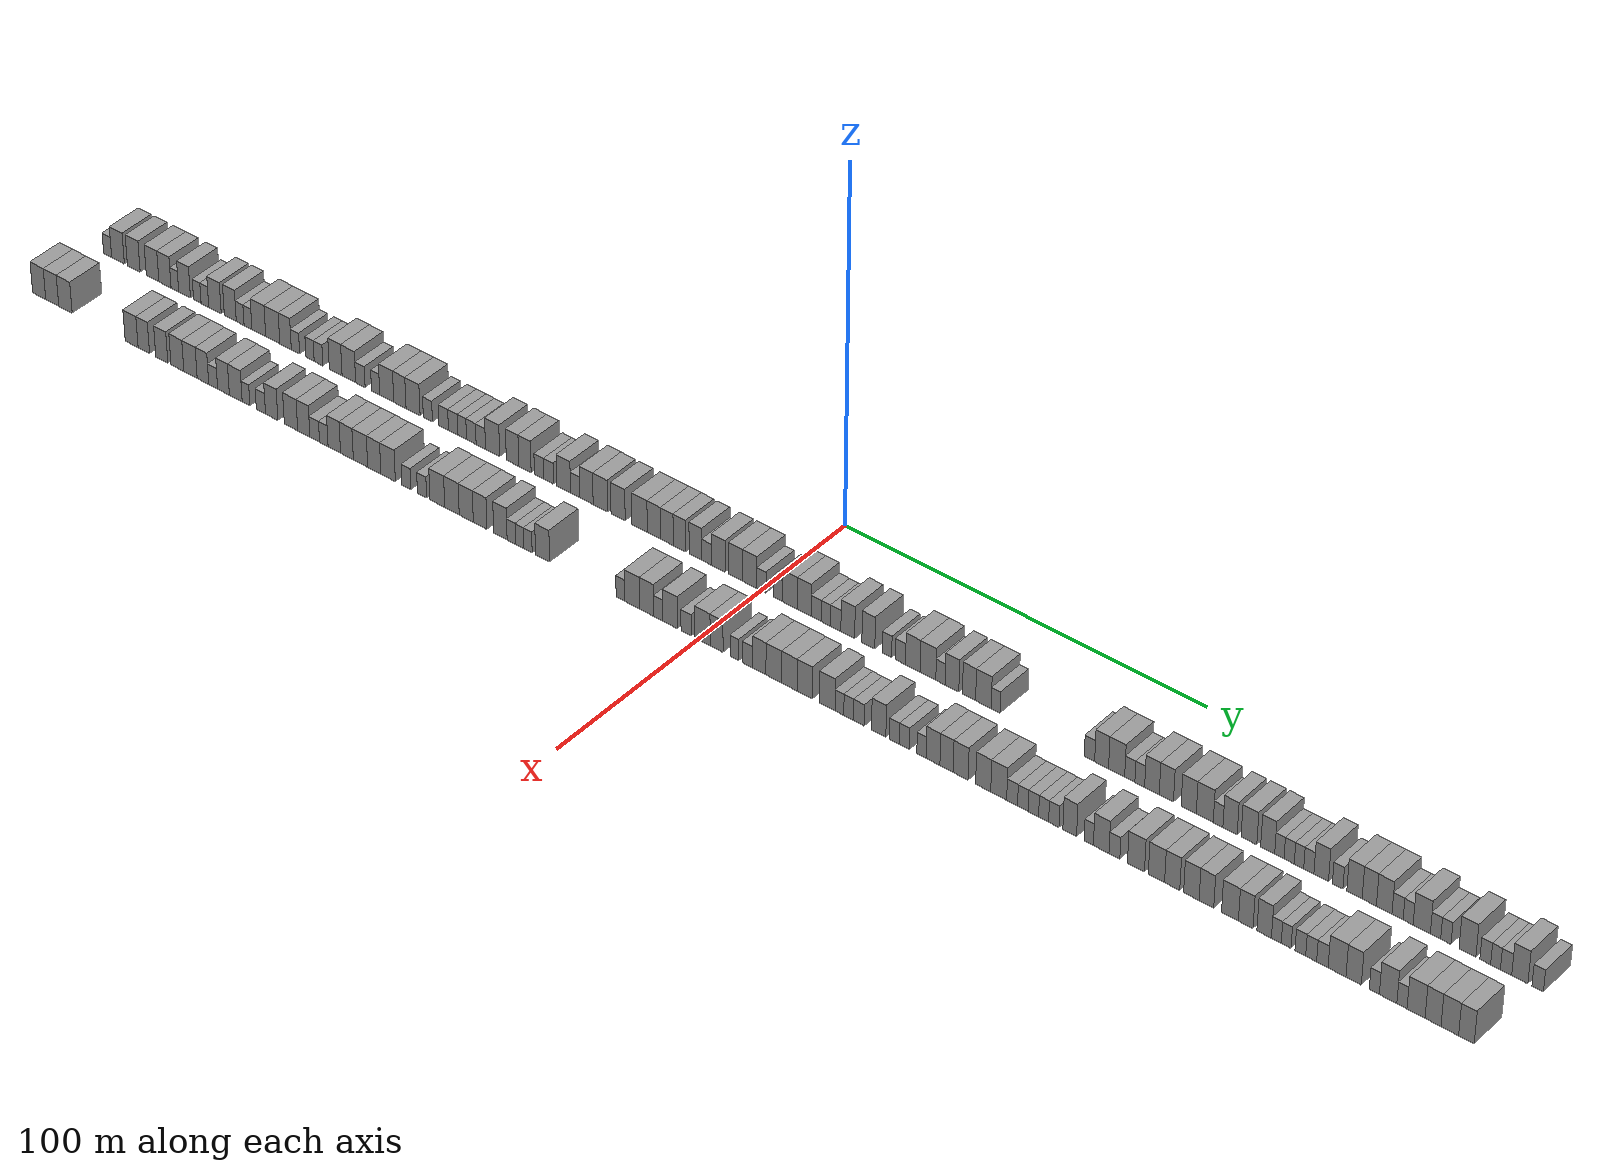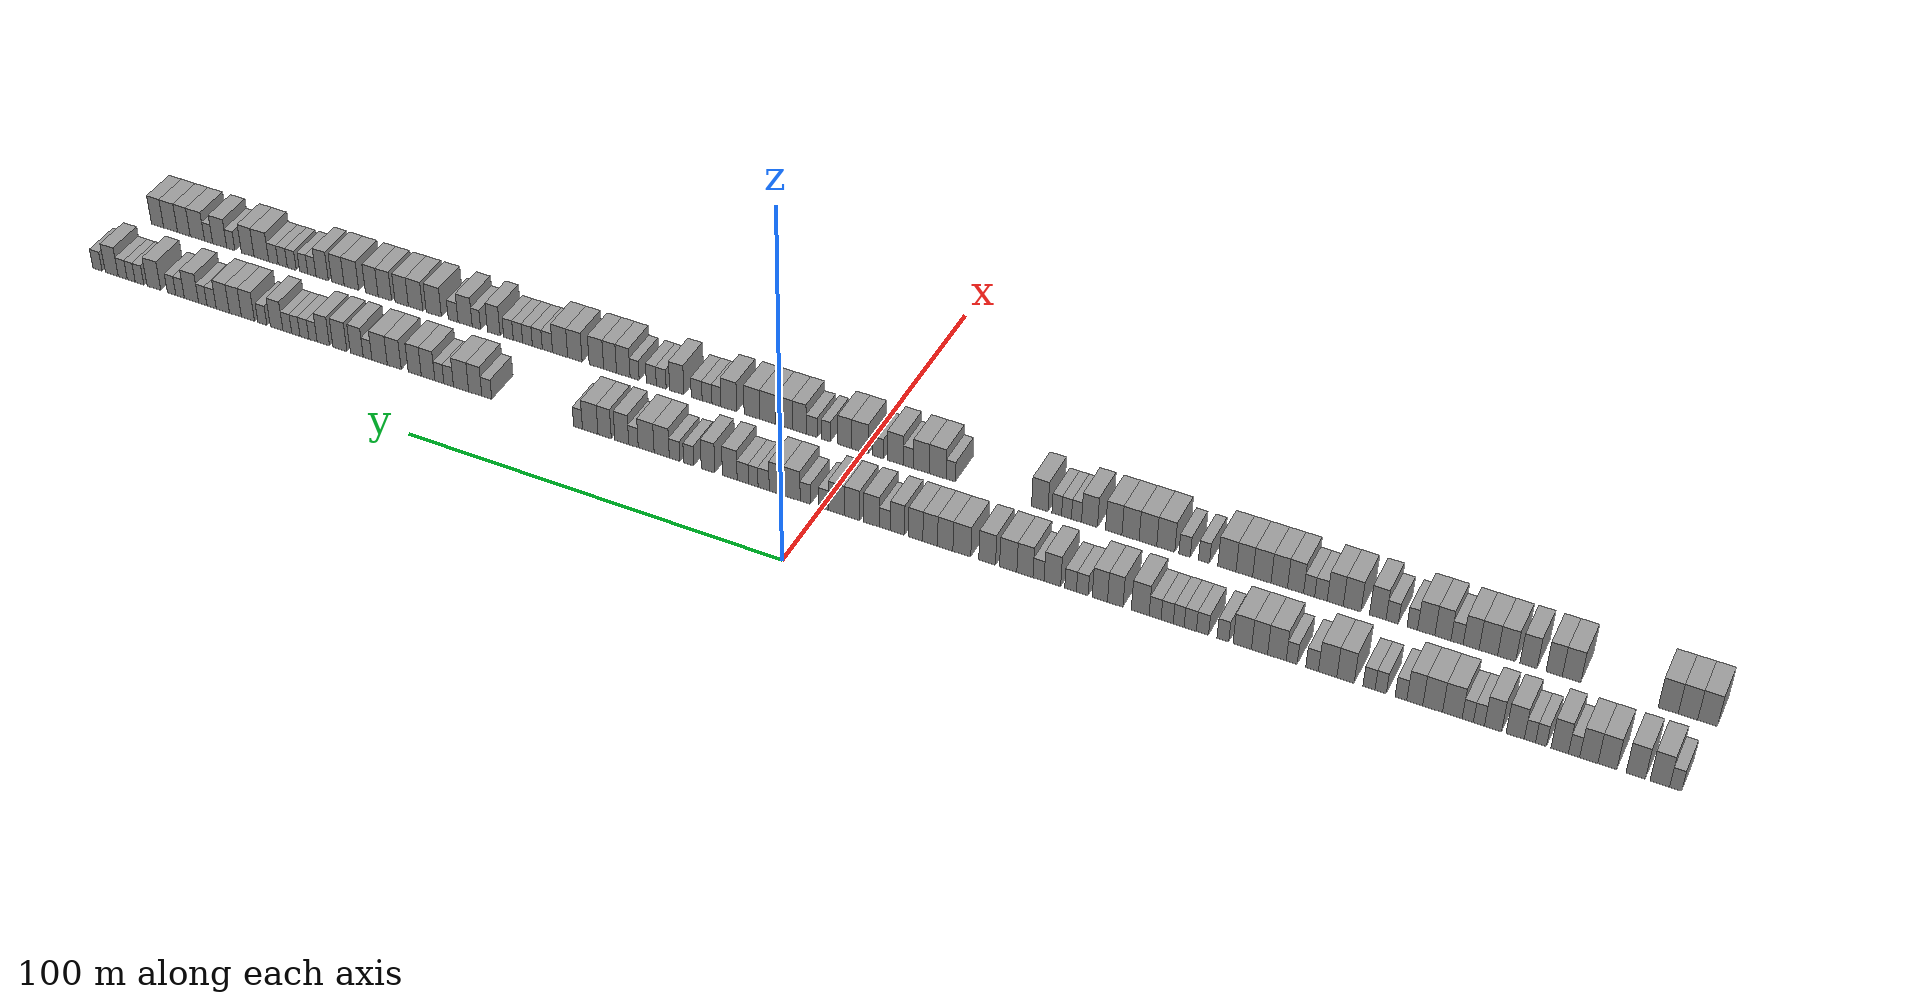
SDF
<sdf version="1.6">
 <world name="default">
  <scene>
   <sky><clouds><speed>12</speed></clouds></sky>
   <ambient>0.4 0.4 0.4 1</ambient>
   <background>0.7 0.7 0.7 1</background>
   <shadows>1</shadows>
  </scene>
  <gravity>0 0 -9.8066</gravity>
  <magnetic_field>6e-06 2.3e-05 -4.2e-05</magnetic_field>
  <physics default="0" name="default_physics" type="ode">
   <ode>
    <solver>
     <type>quick</type>
     <iters>10</iters>
     <sor>1.0</sor>
     <use_dynamic_moi_rescaling>0</use_dynamic_moi_rescaling>
    </solver>
    <constraints>
     <cfm>0</cfm>
     <erp>0.2</erp>
     <contact_max_correcting_vel>100</contact_max_correcting_vel>
     <contact_surface_layer>0.001</contact_surface_layer>
    </constraints>
   </ode>
   <max_step_size>0.004</max_step_size>
   <real_time_factor>1</real_time_factor>
   <real_time_update_rate>250</real_time_update_rate>
  </physics>
  <light name="sun" type="directional">
   <pose>0 0 10 0 0 0</pose>
   <diffuse>0.8 0.8 0.8 1</diffuse>
   <specular>0.2 0.2 0.2 1</specular>
   <attenuation>
    <range>1000</range>
    <constant>0.9</constant>
    <linear>0.01</linear>
    <quadratic>0.001</quadratic>
   </attenuation>
   <direction>-0.5 0.1 -0.9</direction>
  </light>
  <model name="building_1">
   <static>1</static>
   <pose>25.0000 -200.6891 0 0.000000 0.000000 0.000000</pose>
   <link name="link">
    <pose>0 0 3.00 0 0 0</pose>
    <collision name="collision"><geometry><box><size>10.0000 2.6218 6.0000</size></box></geometry></collision>
    <visual name="visual">
     <cast_shadows>0</cast_shadows>
     <geometry><box><size>10.0000 2.6218 6.0000</size></box></geometry>
     <material>
      <script>
       <uri>model://grey_wall/materials/scripts</uri>
       <uri>model://grey_wall/materials/textures</uri>
       <name>vrc/grey_wall</name>
      </script>
     </material>
    </visual>
   </link>
  </model>
  <model name="building_2">
   <static>1</static>
   <pose>25.0000 -197.2870 0 0.000000 0.000000 0.000000</pose>
   <link name="link">
    <pose>0 0 4.50 0 0 0</pose>
    <collision name="collision"><geometry><box><size>10.0000 4.1824 9.0000</size></box></geometry></collision>
    <visual name="visual">
     <cast_shadows>0</cast_shadows>
     <geometry><box><size>10.0000 4.1824 9.0000</size></box></geometry>
     <material>
      <script>
       <uri>model://grey_wall/materials/scripts</uri>
       <uri>model://grey_wall/materials/textures</uri>
       <name>vrc/grey_wall</name>
      </script>
     </material>
    </visual>
   </link>
  </model>
  <model name="building_3">
   <static>1</static>
   <pose>25.0000 -192.1201 0 0.000000 0.000000 0.000000</pose>
   <link name="link">
    <pose>0 0 4.50 0 0 0</pose>
    <collision name="collision"><geometry><box><size>10.0000 4.1514 9.0000</size></box></geometry></collision>
    <visual name="visual">
     <cast_shadows>0</cast_shadows>
     <geometry><box><size>10.0000 4.1514 9.0000</size></box></geometry>
     <material>
      <script>
       <uri>model://grey_wall/materials/scripts</uri>
       <uri>model://grey_wall/materials/textures</uri>
       <name>vrc/grey_wall</name>
      </script>
     </material>
    </visual>
   </link>
  </model>
  <model name="building_4">
   <static>1</static>
   <pose>25.0000 -185.9952 0 0.000000 0.000000 0.000000</pose>
   <link name="link">
    <pose>0 0 4.50 0 0 0</pose>
    <collision name="collision"><geometry><box><size>10.0000 4.0984 9.0000</size></box></geometry></collision>
    <visual name="visual">
     <cast_shadows>0</cast_shadows>
     <geometry><box><size>10.0000 4.0984 9.0000</size></box></geometry>
     <material>
      <script>
       <uri>model://grey_wall/materials/scripts</uri>
       <uri>model://grey_wall/materials/textures</uri>
       <name>vrc/grey_wall</name>
      </script>
     </material>
    </visual>
   </link>
  </model>
  <model name="building_5">
   <static>1</static>
   <pose>25.0000 -181.9679 0 0.000000 0.000000 0.000000</pose>
   <link name="link">
    <pose>0 0 4.50 0 0 0</pose>
    <collision name="collision"><geometry><box><size>10.0000 3.9561 9.0000</size></box></geometry></collision>
    <visual name="visual">
     <cast_shadows>0</cast_shadows>
     <geometry><box><size>10.0000 3.9561 9.0000</size></box></geometry>
     <material>
      <script>
       <uri>model://grey_wall/materials/scripts</uri>
       <uri>model://grey_wall/materials/textures</uri>
       <name>vrc/grey_wall</name>
      </script>
     </material>
    </visual>
   </link>
  </model>
  <model name="building_6">
   <static>1</static>
   <pose>25.0000 -178.7578 0 0.000000 0.000000 0.000000</pose>
   <link name="link">
    <pose>0 0 3.00 0 0 0</pose>
    <collision name="collision"><geometry><box><size>10.0000 2.4642 6.0000</size></box></geometry></collision>
    <visual name="visual">
     <cast_shadows>0</cast_shadows>
     <geometry><box><size>10.0000 2.4642 6.0000</size></box></geometry>
     <material>
      <script>
       <uri>model://grey_wall/materials/scripts</uri>
       <uri>model://grey_wall/materials/textures</uri>
       <name>vrc/grey_wall</name>
      </script>
     </material>
    </visual>
   </link>
  </model>
  <model name="building_7">
   <static>1</static>
   <pose>25.0000 -175.6219 0 0.000000 0.000000 0.000000</pose>
   <link name="link">
    <pose>0 0 4.50 0 0 0</pose>
    <collision name="collision"><geometry><box><size>10.0000 3.8075 9.0000</size></box></geometry></collision>
    <visual name="visual">
     <cast_shadows>0</cast_shadows>
     <geometry><box><size>10.0000 3.8075 9.0000</size></box></geometry>
     <material>
      <script>
       <uri>model://grey_wall/materials/scripts</uri>
       <uri>model://grey_wall/materials/textures</uri>
       <name>vrc/grey_wall</name>
      </script>
     </material>
    </visual>
   </link>
  </model>
  <model name="building_8">
   <static>1</static>
   <pose>25.0000 -171.5128 0 0.000000 0.000000 0.000000</pose>
   <link name="link">
    <pose>0 0 3.00 0 0 0</pose>
    <collision name="collision"><geometry><box><size>10.0000 2.4107 6.0000</size></box></geometry></collision>
    <visual name="visual">
     <cast_shadows>0</cast_shadows>
     <geometry><box><size>10.0000 2.4107 6.0000</size></box></geometry>
     <material>
      <script>
       <uri>model://grey_wall/materials/scripts</uri>
       <uri>model://grey_wall/materials/textures</uri>
       <name>vrc/grey_wall</name>
      </script>
     </material>
    </visual>
   </link>
  </model>
  <model name="building_9">
   <static>1</static>
   <pose>25.0000 -169.0757 0 0.000000 0.000000 0.000000</pose>
   <link name="link">
    <pose>0 0 3.00 0 0 0</pose>
    <collision name="collision"><geometry><box><size>10.0000 2.4634 6.0000</size></box></geometry></collision>
    <visual name="visual">
     <cast_shadows>0</cast_shadows>
     <geometry><box><size>10.0000 2.4634 6.0000</size></box></geometry>
     <material>
      <script>
       <uri>model://grey_wall/materials/scripts</uri>
       <uri>model://grey_wall/materials/textures</uri>
       <name>vrc/grey_wall</name>
      </script>
     </material>
    </visual>
   </link>
  </model>
  <model name="building_10">
   <static>1</static>
   <pose>25.0000 -165.8358 0 0.000000 0.000000 0.000000</pose>
   <link name="link">
    <pose>0 0 4.50 0 0 0</pose>
    <collision name="collision"><geometry><box><size>10.0000 4.0163 9.0000</size></box></geometry></collision>
    <visual name="visual">
     <cast_shadows>0</cast_shadows>
     <geometry><box><size>10.0000 4.0163 9.0000</size></box></geometry>
     <material>
      <script>
       <uri>model://grey_wall/materials/scripts</uri>
       <uri>model://grey_wall/materials/textures</uri>
       <name>vrc/grey_wall</name>
      </script>
     </material>
    </visual>
   </link>
  </model>
  <model name="building_11">
   <static>1</static>
   <pose>25.0000 -160.9196 0 0.000000 0.000000 0.000000</pose>
   <link name="link">
    <pose>0 0 4.50 0 0 0</pose>
    <collision name="collision"><geometry><box><size>10.0000 3.8163 9.0000</size></box></geometry></collision>
    <visual name="visual">
     <cast_shadows>0</cast_shadows>
     <geometry><box><size>10.0000 3.8163 9.0000</size></box></geometry>
     <material>
      <script>
       <uri>model://grey_wall/materials/scripts</uri>
       <uri>model://grey_wall/materials/textures</uri>
       <name>vrc/grey_wall</name>
      </script>
     </material>
    </visual>
   </link>
  </model>
  <model name="building_12">
   <static>1</static>
   <pose>25.0000 -157.7685 0 0.000000 0.000000 0.000000</pose>
   <link name="link">
    <pose>0 0 3.00 0 0 0</pose>
    <collision name="collision"><geometry><box><size>10.0000 2.4858 6.0000</size></box></geometry></collision>
    <visual name="visual">
     <cast_shadows>0</cast_shadows>
     <geometry><box><size>10.0000 2.4858 6.0000</size></box></geometry>
     <material>
      <script>
       <uri>model://grey_wall/materials/scripts</uri>
       <uri>model://grey_wall/materials/textures</uri>
       <name>vrc/grey_wall</name>
      </script>
     </material>
    </visual>
   </link>
  </model>
  <model name="building_13">
   <static>1</static>
   <pose>25.0000 -155.2720 0 0.000000 0.000000 0.000000</pose>
   <link name="link">
    <pose>0 0 3.00 0 0 0</pose>
    <collision name="collision"><geometry><box><size>10.0000 2.5074 6.0000</size></box></geometry></collision>
    <visual name="visual">
     <cast_shadows>0</cast_shadows>
     <geometry><box><size>10.0000 2.5074 6.0000</size></box></geometry>
     <material>
      <script>
       <uri>model://grey_wall/materials/scripts</uri>
       <uri>model://grey_wall/materials/textures</uri>
       <name>vrc/grey_wall</name>
      </script>
     </material>
    </visual>
   </link>
  </model>
  <model name="building_14">
   <static>1</static>
   <pose>25.0000 -151.8228 0 0.000000 0.000000 0.000000</pose>
   <link name="link">
    <pose>0 0 4.50 0 0 0</pose>
    <collision name="collision"><geometry><box><size>10.0000 4.3909 9.0000</size></box></geometry></collision>
    <visual name="visual">
     <cast_shadows>0</cast_shadows>
     <geometry><box><size>10.0000 4.3909 9.0000</size></box></geometry>
     <material>
      <script>
       <uri>model://grey_wall/materials/scripts</uri>
       <uri>model://grey_wall/materials/textures</uri>
       <name>vrc/grey_wall</name>
      </script>
     </material>
    </visual>
   </link>
  </model>
  <model name="building_15">
   <static>1</static>
   <pose>25.0000 -147.3984 0 0.000000 0.000000 0.000000</pose>
   <link name="link">
    <pose>0 0 4.50 0 0 0</pose>
    <collision name="collision"><geometry><box><size>10.0000 4.4581 9.0000</size></box></geometry></collision>
    <visual name="visual">
     <cast_shadows>0</cast_shadows>
     <geometry><box><size>10.0000 4.4581 9.0000</size></box></geometry>
     <material>
      <script>
       <uri>model://grey_wall/materials/scripts</uri>
       <uri>model://grey_wall/materials/textures</uri>
       <name>vrc/grey_wall</name>
      </script>
     </material>
    </visual>
   </link>
  </model>
  <model name="building_16">
   <static>1</static>
   <pose>25.0000 -143.3528 0 0.000000 0.000000 0.000000</pose>
   <link name="link">
    <pose>0 0 4.50 0 0 0</pose>
    <collision name="collision"><geometry><box><size>10.0000 3.6331 9.0000</size></box></geometry></collision>
    <visual name="visual">
     <cast_shadows>0</cast_shadows>
     <geometry><box><size>10.0000 3.6331 9.0000</size></box></geometry>
     <material>
      <script>
       <uri>model://grey_wall/materials/scripts</uri>
       <uri>model://grey_wall/materials/textures</uri>
       <name>vrc/grey_wall</name>
      </script>
     </material>
    </visual>
   </link>
  </model>
  <model name="building_17">
   <static>1</static>
   <pose>25.0000 -140.2241 0 0.000000 0.000000 0.000000</pose>
   <link name="link">
    <pose>0 0 3.00 0 0 0</pose>
    <collision name="collision"><geometry><box><size>10.0000 2.6244 6.0000</size></box></geometry></collision>
    <visual name="visual">
     <cast_shadows>0</cast_shadows>
     <geometry><box><size>10.0000 2.6244 6.0000</size></box></geometry>
     <material>
      <script>
       <uri>model://grey_wall/materials/scripts</uri>
       <uri>model://grey_wall/materials/textures</uri>
       <name>vrc/grey_wall</name>
      </script>
     </material>
    </visual>
   </link>
  </model>
  <model name="building_18">
   <static>1</static>
   <pose>25.0000 -135.6285 0 0.000000 0.000000 0.000000</pose>
   <link name="link">
    <pose>0 0 3.00 0 0 0</pose>
    <collision name="collision"><geometry><box><size>10.0000 2.5668 6.0000</size></box></geometry></collision>
    <visual name="visual">
     <cast_shadows>0</cast_shadows>
     <geometry><box><size>10.0000 2.5668 6.0000</size></box></geometry>
     <material>
      <script>
       <uri>model://grey_wall/materials/scripts</uri>
       <uri>model://grey_wall/materials/textures</uri>
       <name>vrc/grey_wall</name>
      </script>
     </material>
    </visual>
   </link>
  </model>
  <model name="building_19">
   <static>1</static>
   <pose>25.0000 -132.9644 0 0.000000 0.000000 0.000000</pose>
   <link name="link">
    <pose>0 0 3.00 0 0 0</pose>
    <collision name="collision"><geometry><box><size>10.0000 2.7615 6.0000</size></box></geometry></collision>
    <visual name="visual">
     <cast_shadows>0</cast_shadows>
     <geometry><box><size>10.0000 2.7615 6.0000</size></box></geometry>
     <material>
      <script>
       <uri>model://grey_wall/materials/scripts</uri>
       <uri>model://grey_wall/materials/textures</uri>
       <name>vrc/grey_wall</name>
      </script>
     </material>
    </visual>
   </link>
  </model>
  <model name="building_20">
   <static>1</static>
   <pose>25.0000 -127.5885 0 0.000000 0.000000 0.000000</pose>
   <link name="link">
    <pose>0 0 4.50 0 0 0</pose>
    <collision name="collision"><geometry><box><size>10.0000 3.9903 9.0000</size></box></geometry></collision>
    <visual name="visual">
     <cast_shadows>0</cast_shadows>
     <geometry><box><size>10.0000 3.9903 9.0000</size></box></geometry>
     <material>
      <script>
       <uri>model://grey_wall/materials/scripts</uri>
       <uri>model://grey_wall/materials/textures</uri>
       <name>vrc/grey_wall</name>
      </script>
     </material>
    </visual>
   </link>
  </model>
  <model name="building_21">
   <static>1</static>
   <pose>25.0000 -123.4686 0 0.000000 0.000000 0.000000</pose>
   <link name="link">
    <pose>0 0 4.50 0 0 0</pose>
    <collision name="collision"><geometry><box><size>10.0000 4.2495 9.0000</size></box></geometry></collision>
    <visual name="visual">
     <cast_shadows>0</cast_shadows>
     <geometry><box><size>10.0000 4.2495 9.0000</size></box></geometry>
     <material>
      <script>
       <uri>model://grey_wall/materials/scripts</uri>
       <uri>model://grey_wall/materials/textures</uri>
       <name>vrc/grey_wall</name>
      </script>
     </material>
    </visual>
   </link>
  </model>
  <model name="building_22">
   <static>1</static>
   <pose>25.0000 -119.8854 0 0.000000 0.000000 0.000000</pose>
   <link name="link">
    <pose>0 0 3.00 0 0 0</pose>
    <collision name="collision"><geometry><box><size>10.0000 2.9168 6.0000</size></box></geometry></collision>
    <visual name="visual">
     <cast_shadows>0</cast_shadows>
     <geometry><box><size>10.0000 2.9168 6.0000</size></box></geometry>
     <material>
      <script>
       <uri>model://grey_wall/materials/scripts</uri>
       <uri>model://grey_wall/materials/textures</uri>
       <name>vrc/grey_wall</name>
      </script>
     </material>
    </visual>
   </link>
  </model>
  <model name="building_23">
   <static>1</static>
   <pose>25.0000 -115.1533 0 0.000000 0.000000 0.000000</pose>
   <link name="link">
    <pose>0 0 3.00 0 0 0</pose>
    <collision name="collision"><geometry><box><size>10.0000 2.5473 6.0000</size></box></geometry></collision>
    <visual name="visual">
     <cast_shadows>0</cast_shadows>
     <geometry><box><size>10.0000 2.5473 6.0000</size></box></geometry>
     <material>
      <script>
       <uri>model://grey_wall/materials/scripts</uri>
       <uri>model://grey_wall/materials/textures</uri>
       <name>vrc/grey_wall</name>
      </script>
     </material>
    </visual>
   </link>
  </model>
  <model name="building_24">
   <static>1</static>
   <pose>25.0000 -111.7035 0 0.000000 0.000000 0.000000</pose>
   <link name="link">
    <pose>0 0 4.50 0 0 0</pose>
    <collision name="collision"><geometry><box><size>10.0000 4.3524 9.0000</size></box></geometry></collision>
    <visual name="visual">
     <cast_shadows>0</cast_shadows>
     <geometry><box><size>10.0000 4.3524 9.0000</size></box></geometry>
     <material>
      <script>
       <uri>model://grey_wall/materials/scripts</uri>
       <uri>model://grey_wall/materials/textures</uri>
       <name>vrc/grey_wall</name>
      </script>
     </material>
    </visual>
   </link>
  </model>
  <model name="building_25">
   <static>1</static>
   <pose>25.0000 -107.6400 0 0.000000 0.000000 0.000000</pose>
   <link name="link">
    <pose>0 0 4.50 0 0 0</pose>
    <collision name="collision"><geometry><box><size>10.0000 3.7747 9.0000</size></box></geometry></collision>
    <visual name="visual">
     <cast_shadows>0</cast_shadows>
     <geometry><box><size>10.0000 3.7747 9.0000</size></box></geometry>
     <material>
      <script>
       <uri>model://grey_wall/materials/scripts</uri>
       <uri>model://grey_wall/materials/textures</uri>
       <name>vrc/grey_wall</name>
      </script>
     </material>
    </visual>
   </link>
  </model>
  <model name="building_26">
   <static>1</static>
   <pose>25.0000 -103.5955 0 0.000000 0.000000 0.000000</pose>
   <link name="link">
    <pose>0 0 4.50 0 0 0</pose>
    <collision name="collision"><geometry><box><size>10.0000 4.3142 9.0000</size></box></geometry></collision>
    <visual name="visual">
     <cast_shadows>0</cast_shadows>
     <geometry><box><size>10.0000 4.3142 9.0000</size></box></geometry>
     <material>
      <script>
       <uri>model://grey_wall/materials/scripts</uri>
       <uri>model://grey_wall/materials/textures</uri>
       <name>vrc/grey_wall</name>
      </script>
     </material>
    </visual>
   </link>
  </model>
  <model name="building_27">
   <static>1</static>
   <pose>25.0000 -99.0458 0 0.000000 0.000000 0.000000</pose>
   <link name="link">
    <pose>0 0 3.00 0 0 0</pose>
    <collision name="collision"><geometry><box><size>10.0000 2.7853 6.0000</size></box></geometry></collision>
    <visual name="visual">
     <cast_shadows>0</cast_shadows>
     <geometry><box><size>10.0000 2.7853 6.0000</size></box></geometry>
     <material>
      <script>
       <uri>model://grey_wall/materials/scripts</uri>
       <uri>model://grey_wall/materials/textures</uri>
       <name>vrc/grey_wall</name>
      </script>
     </material>
    </visual>
   </link>
  </model>
  <model name="building_28">
   <static>1</static>
   <pose>25.0000 -94.2055 0 0.000000 0.000000 0.000000</pose>
   <link name="link">
    <pose>0 0 3.00 0 0 0</pose>
    <collision name="collision"><geometry><box><size>10.0000 2.8954 6.0000</size></box></geometry></collision>
    <visual name="visual">
     <cast_shadows>0</cast_shadows>
     <geometry><box><size>10.0000 2.8954 6.0000</size></box></geometry>
     <material>
      <script>
       <uri>model://grey_wall/materials/scripts</uri>
       <uri>model://grey_wall/materials/textures</uri>
       <name>vrc/grey_wall</name>
      </script>
     </material>
    </visual>
   </link>
  </model>
  <model name="building_29">
   <static>1</static>
   <pose>25.0000 -91.2992 0 0.000000 0.000000 0.000000</pose>
   <link name="link">
    <pose>0 0 3.00 0 0 0</pose>
    <collision name="collision"><geometry><box><size>10.0000 2.9172 6.0000</size></box></geometry></collision>
    <visual name="visual">
     <cast_shadows>0</cast_shadows>
     <geometry><box><size>10.0000 2.9172 6.0000</size></box></geometry>
     <material>
      <script>
       <uri>model://grey_wall/materials/scripts</uri>
       <uri>model://grey_wall/materials/textures</uri>
       <name>vrc/grey_wall</name>
      </script>
     </material>
    </visual>
   </link>
  </model>
  <model name="building_30">
   <static>1</static>
   <pose>25.0000 -88.5461 0 0.000000 0.000000 0.000000</pose>
   <link name="link">
    <pose>0 0 3.00 0 0 0</pose>
    <collision name="collision"><geometry><box><size>10.0000 2.5892 6.0000</size></box></geometry></collision>
    <visual name="visual">
     <cast_shadows>0</cast_shadows>
     <geometry><box><size>10.0000 2.5892 6.0000</size></box></geometry>
     <material>
      <script>
       <uri>model://grey_wall/materials/scripts</uri>
       <uri>model://grey_wall/materials/textures</uri>
       <name>vrc/grey_wall</name>
      </script>
     </material>
    </visual>
   </link>
  </model>
  <model name="building_31">
   <static>1</static>
   <pose>25.0000 -85.7914 0 0.000000 0.000000 0.000000</pose>
   <link name="link">
    <pose>0 0 3.00 0 0 0</pose>
    <collision name="collision"><geometry><box><size>10.0000 2.9202 6.0000</size></box></geometry></collision>
    <visual name="visual">
     <cast_shadows>0</cast_shadows>
     <geometry><box><size>10.0000 2.9202 6.0000</size></box></geometry>
     <material>
      <script>
       <uri>model://grey_wall/materials/scripts</uri>
       <uri>model://grey_wall/materials/textures</uri>
       <name>vrc/grey_wall</name>
      </script>
     </material>
    </visual>
   </link>
  </model>
  <model name="building_32">
   <static>1</static>
   <pose>25.0000 -82.9009 0 0.000000 0.000000 0.000000</pose>
   <link name="link">
    <pose>0 0 3.00 0 0 0</pose>
    <collision name="collision"><geometry><box><size>10.0000 2.8608 6.0000</size></box></geometry></collision>
    <visual name="visual">
     <cast_shadows>0</cast_shadows>
     <geometry><box><size>10.0000 2.8608 6.0000</size></box></geometry>
     <material>
      <script>
       <uri>model://grey_wall/materials/scripts</uri>
       <uri>model://grey_wall/materials/textures</uri>
       <name>vrc/grey_wall</name>
      </script>
     </material>
    </visual>
   </link>
  </model>
  <model name="building_33">
   <static>1</static>
   <pose>25.0000 -79.3252 0 0.000000 0.000000 0.000000</pose>
   <link name="link">
    <pose>0 0 4.50 0 0 0</pose>
    <collision name="collision"><geometry><box><size>10.0000 4.2905 9.0000</size></box></geometry></collision>
    <visual name="visual">
     <cast_shadows>0</cast_shadows>
     <geometry><box><size>10.0000 4.2905 9.0000</size></box></geometry>
     <material>
      <script>
       <uri>model://grey_wall/materials/scripts</uri>
       <uri>model://grey_wall/materials/textures</uri>
       <name>vrc/grey_wall</name>
      </script>
     </material>
    </visual>
   </link>
  </model>
  <model name="building_34">
   <static>1</static>
   <pose>25.0000 -73.3015 0 0.000000 0.000000 0.000000</pose>
   <link name="link">
    <pose>0 0 4.50 0 0 0</pose>
    <collision name="collision"><geometry><box><size>10.0000 3.7569 9.0000</size></box></geometry></collision>
    <visual name="visual">
     <cast_shadows>0</cast_shadows>
     <geometry><box><size>10.0000 3.7569 9.0000</size></box></geometry>
     <material>
      <script>
       <uri>model://grey_wall/materials/scripts</uri>
       <uri>model://grey_wall/materials/textures</uri>
       <name>vrc/grey_wall</name>
      </script>
     </material>
    </visual>
   </link>
  </model>
  <model name="building_35">
   <static>1</static>
   <pose>25.0000 -69.5739 0 0.000000 0.000000 0.000000</pose>
   <link name="link">
    <pose>0 0 4.50 0 0 0</pose>
    <collision name="collision"><geometry><box><size>10.0000 3.6982 9.0000</size></box></geometry></collision>
    <visual name="visual">
     <cast_shadows>0</cast_shadows>
     <geometry><box><size>10.0000 3.6982 9.0000</size></box></geometry>
     <material>
      <script>
       <uri>model://grey_wall/materials/scripts</uri>
       <uri>model://grey_wall/materials/textures</uri>
       <name>vrc/grey_wall</name>
      </script>
     </material>
    </visual>
   </link>
  </model>
  <model name="building_36">
   <static>1</static>
   <pose>25.0000 -65.3007 0 0.000000 0.000000 0.000000</pose>
   <link name="link">
    <pose>0 0 3.00 0 0 0</pose>
    <collision name="collision"><geometry><box><size>10.0000 2.8482 6.0000</size></box></geometry></collision>
    <visual name="visual">
     <cast_shadows>0</cast_shadows>
     <geometry><box><size>10.0000 2.8482 6.0000</size></box></geometry>
     <material>
      <script>
       <uri>model://grey_wall/materials/scripts</uri>
       <uri>model://grey_wall/materials/textures</uri>
       <name>vrc/grey_wall</name>
      </script>
     </material>
    </visual>
   </link>
  </model>
  <model name="building_37">
   <static>1</static>
   <pose>25.0000 -62.4495 0 0.000000 0.000000 0.000000</pose>
   <link name="link">
    <pose>0 0 3.00 0 0 0</pose>
    <collision name="collision"><geometry><box><size>10.0000 2.8541 6.0000</size></box></geometry></collision>
    <visual name="visual">
     <cast_shadows>0</cast_shadows>
     <geometry><box><size>10.0000 2.8541 6.0000</size></box></geometry>
     <material>
      <script>
       <uri>model://grey_wall/materials/scripts</uri>
       <uri>model://grey_wall/materials/textures</uri>
       <name>vrc/grey_wall</name>
      </script>
     </material>
    </visual>
   </link>
  </model>
  <model name="building_38">
   <static>1</static>
   <pose>25.0000 -57.9823 0 0.000000 0.000000 0.000000</pose>
   <link name="link">
    <pose>0 0 4.50 0 0 0</pose>
    <collision name="collision"><geometry><box><size>10.0000 4.0803 9.0000</size></box></geometry></collision>
    <visual name="visual">
     <cast_shadows>0</cast_shadows>
     <geometry><box><size>10.0000 4.0803 9.0000</size></box></geometry>
     <material>
      <script>
       <uri>model://grey_wall/materials/scripts</uri>
       <uri>model://grey_wall/materials/textures</uri>
       <name>vrc/grey_wall</name>
      </script>
     </material>
    </visual>
   </link>
  </model>
  <model name="building_39">
   <static>1</static>
   <pose>25.0000 -54.5782 0 0.000000 0.000000 0.000000</pose>
   <link name="link">
    <pose>0 0 3.00 0 0 0</pose>
    <collision name="collision"><geometry><box><size>10.0000 2.7280 6.0000</size></box></geometry></collision>
    <visual name="visual">
     <cast_shadows>0</cast_shadows>
     <geometry><box><size>10.0000 2.7280 6.0000</size></box></geometry>
     <material>
      <script>
       <uri>model://grey_wall/materials/scripts</uri>
       <uri>model://grey_wall/materials/textures</uri>
       <name>vrc/grey_wall</name>
      </script>
     </material>
    </visual>
   </link>
  </model>
  <model name="building_40">
   <static>1</static>
   <pose>25.0000 -51.2221 0 0.000000 0.000000 0.000000</pose>
   <link name="link">
    <pose>0 0 4.50 0 0 0</pose>
    <collision name="collision"><geometry><box><size>10.0000 3.9841 9.0000</size></box></geometry></collision>
    <visual name="visual">
     <cast_shadows>0</cast_shadows>
     <geometry><box><size>10.0000 3.9841 9.0000</size></box></geometry>
     <material>
      <script>
       <uri>model://grey_wall/materials/scripts</uri>
       <uri>model://grey_wall/materials/textures</uri>
       <name>vrc/grey_wall</name>
      </script>
     </material>
    </visual>
   </link>
  </model>
  <model name="building_41">
   <static>1</static>
   <pose>25.0000 -47.0854 0 0.000000 0.000000 0.000000</pose>
   <link name="link">
    <pose>0 0 4.50 0 0 0</pose>
    <collision name="collision"><geometry><box><size>10.0000 4.2894 9.0000</size></box></geometry></collision>
    <visual name="visual">
     <cast_shadows>0</cast_shadows>
     <geometry><box><size>10.0000 4.2894 9.0000</size></box></geometry>
     <material>
      <script>
       <uri>model://grey_wall/materials/scripts</uri>
       <uri>model://grey_wall/materials/textures</uri>
       <name>vrc/grey_wall</name>
      </script>
     </material>
    </visual>
   </link>
  </model>
  <model name="building_42">
   <static>1</static>
   <pose>25.0000 -41.8532 0 0.000000 0.000000 0.000000</pose>
   <link name="link">
    <pose>0 0 4.50 0 0 0</pose>
    <collision name="collision"><geometry><box><size>10.0000 4.1750 9.0000</size></box></geometry></collision>
    <visual name="visual">
     <cast_shadows>0</cast_shadows>
     <geometry><box><size>10.0000 4.1750 9.0000</size></box></geometry>
     <material>
      <script>
       <uri>model://grey_wall/materials/scripts</uri>
       <uri>model://grey_wall/materials/textures</uri>
       <name>vrc/grey_wall</name>
      </script>
     </material>
    </visual>
   </link>
  </model>
  <model name="building_43">
   <static>1</static>
   <pose>25.0000 -35.5196 0 0.000000 0.000000 0.000000</pose>
   <link name="link">
    <pose>0 0 4.50 0 0 0</pose>
    <collision name="collision"><geometry><box><size>10.0000 4.4922 9.0000</size></box></geometry></collision>
    <visual name="visual">
     <cast_shadows>0</cast_shadows>
     <geometry><box><size>10.0000 4.4922 9.0000</size></box></geometry>
     <material>
      <script>
       <uri>model://grey_wall/materials/scripts</uri>
       <uri>model://grey_wall/materials/textures</uri>
       <name>vrc/grey_wall</name>
      </script>
     </material>
    </visual>
   </link>
  </model>
  <model name="building_44">
   <static>1</static>
   <pose>25.0000 -31.3297 0 0.000000 0.000000 0.000000</pose>
   <link name="link">
    <pose>0 0 4.50 0 0 0</pose>
    <collision name="collision"><geometry><box><size>10.0000 3.8875 9.0000</size></box></geometry></collision>
    <visual name="visual">
     <cast_shadows>0</cast_shadows>
     <geometry><box><size>10.0000 3.8875 9.0000</size></box></geometry>
     <material>
      <script>
       <uri>model://grey_wall/materials/scripts</uri>
       <uri>model://grey_wall/materials/textures</uri>
       <name>vrc/grey_wall</name>
      </script>
     </material>
    </visual>
   </link>
  </model>
  <model name="building_45">
   <static>1</static>
   <pose>25.0000 -27.5345 0 0.000000 0.000000 0.000000</pose>
   <link name="link">
    <pose>0 0 4.50 0 0 0</pose>
    <collision name="collision"><geometry><box><size>10.0000 3.7029 9.0000</size></box></geometry></collision>
    <visual name="visual">
     <cast_shadows>0</cast_shadows>
     <geometry><box><size>10.0000 3.7029 9.0000</size></box></geometry>
     <material>
      <script>
       <uri>model://grey_wall/materials/scripts</uri>
       <uri>model://grey_wall/materials/textures</uri>
       <name>vrc/grey_wall</name>
      </script>
     </material>
    </visual>
   </link>
  </model>
  <model name="building_46">
   <static>1</static>
   <pose>25.0000 -23.8702 0 0.000000 0.000000 0.000000</pose>
   <link name="link">
    <pose>0 0 4.50 0 0 0</pose>
    <collision name="collision"><geometry><box><size>10.0000 3.6257 9.0000</size></box></geometry></collision>
    <visual name="visual">
     <cast_shadows>0</cast_shadows>
     <geometry><box><size>10.0000 3.6257 9.0000</size></box></geometry>
     <material>
      <script>
       <uri>model://grey_wall/materials/scripts</uri>
       <uri>model://grey_wall/materials/textures</uri>
       <name>vrc/grey_wall</name>
      </script>
     </material>
    </visual>
   </link>
  </model>
  <model name="building_47">
   <static>1</static>
   <pose>25.0000 -19.2437 0 0.000000 0.000000 0.000000</pose>
   <link name="link">
    <pose>0 0 4.50 0 0 0</pose>
    <collision name="collision"><geometry><box><size>10.0000 3.6273 9.0000</size></box></geometry></collision>
    <visual name="visual">
     <cast_shadows>0</cast_shadows>
     <geometry><box><size>10.0000 3.6273 9.0000</size></box></geometry>
     <material>
      <script>
       <uri>model://grey_wall/materials/scripts</uri>
       <uri>model://grey_wall/materials/textures</uri>
       <name>vrc/grey_wall</name>
      </script>
     </material>
    </visual>
   </link>
  </model>
  <model name="building_48">
   <static>1</static>
   <pose>25.0000 -16.0153 0 0.000000 0.000000 0.000000</pose>
   <link name="link">
    <pose>0 0 3.00 0 0 0</pose>
    <collision name="collision"><geometry><box><size>10.0000 2.8296 6.0000</size></box></geometry></collision>
    <visual name="visual">
     <cast_shadows>0</cast_shadows>
     <geometry><box><size>10.0000 2.8296 6.0000</size></box></geometry>
     <material>
      <script>
       <uri>model://grey_wall/materials/scripts</uri>
       <uri>model://grey_wall/materials/textures</uri>
       <name>vrc/grey_wall</name>
      </script>
     </material>
    </visual>
   </link>
  </model>
  <model name="building_49">
   <static>1</static>
   <pose>25.0000 -12.6120 0 0.000000 0.000000 0.000000</pose>
   <link name="link">
    <pose>0 0 4.50 0 0 0</pose>
    <collision name="collision"><geometry><box><size>10.0000 3.9770 9.0000</size></box></geometry></collision>
    <visual name="visual">
     <cast_shadows>0</cast_shadows>
     <geometry><box><size>10.0000 3.9770 9.0000</size></box></geometry>
     <material>
      <script>
       <uri>model://grey_wall/materials/scripts</uri>
       <uri>model://grey_wall/materials/textures</uri>
       <name>vrc/grey_wall</name>
      </script>
     </material>
    </visual>
   </link>
  </model>
  <model name="building_50">
   <static>1</static>
   <pose>25.0000 -7.6137 0 0.000000 0.000000 0.000000</pose>
   <link name="link">
    <pose>0 0 4.50 0 0 0</pose>
    <collision name="collision"><geometry><box><size>10.0000 4.0196 9.0000</size></box></geometry></collision>
    <visual name="visual">
     <cast_shadows>0</cast_shadows>
     <geometry><box><size>10.0000 4.0196 9.0000</size></box></geometry>
     <material>
      <script>
       <uri>model://grey_wall/materials/scripts</uri>
       <uri>model://grey_wall/materials/textures</uri>
       <name>vrc/grey_wall</name>
      </script>
     </material>
    </visual>
   </link>
  </model>
  <model name="building_51">
   <static>1</static>
   <pose>25.0000 -3.5496 0 0.000000 0.000000 0.000000</pose>
   <link name="link">
    <pose>0 0 4.50 0 0 0</pose>
    <collision name="collision"><geometry><box><size>10.0000 4.1087 9.0000</size></box></geometry></collision>
    <visual name="visual">
     <cast_shadows>0</cast_shadows>
     <geometry><box><size>10.0000 4.1087 9.0000</size></box></geometry>
     <material>
      <script>
       <uri>model://grey_wall/materials/scripts</uri>
       <uri>model://grey_wall/materials/textures</uri>
       <name>vrc/grey_wall</name>
      </script>
     </material>
    </visual>
   </link>
  </model>
  <model name="building_52">
   <static>1</static>
   <pose>25.0000 -0.1980 0 0.000000 0.000000 0.000000</pose>
   <link name="link">
    <pose>0 0 3.00 0 0 0</pose>
    <collision name="collision"><geometry><box><size>10.0000 2.5946 6.0000</size></box></geometry></collision>
    <visual name="visual">
     <cast_shadows>0</cast_shadows>
     <geometry><box><size>10.0000 2.5946 6.0000</size></box></geometry>
     <material>
      <script>
       <uri>model://grey_wall/materials/scripts</uri>
       <uri>model://grey_wall/materials/textures</uri>
       <name>vrc/grey_wall</name>
      </script>
     </material>
    </visual>
   </link>
  </model>
  <model name="building_53">
   <static>1</static>
   <pose>25.0000 4.4550 0 0.000000 0.000000 0.000000</pose>
   <link name="link">
    <pose>0 0 3.00 0 0 0</pose>
    <collision name="collision"><geometry><box><size>10.0000 2.7113 6.0000</size></box></geometry></collision>
    <visual name="visual">
     <cast_shadows>0</cast_shadows>
     <geometry><box><size>10.0000 2.7113 6.0000</size></box></geometry>
     <material>
      <script>
       <uri>model://grey_wall/materials/scripts</uri>
       <uri>model://grey_wall/materials/textures</uri>
       <name>vrc/grey_wall</name>
      </script>
     </material>
    </visual>
   </link>
  </model>
  <model name="building_54">
   <static>1</static>
   <pose>25.0000 7.9434 0 0.000000 0.000000 0.000000</pose>
   <link name="link">
    <pose>0 0 4.50 0 0 0</pose>
    <collision name="collision"><geometry><box><size>10.0000 4.2656 9.0000</size></box></geometry></collision>
    <visual name="visual">
     <cast_shadows>0</cast_shadows>
     <geometry><box><size>10.0000 4.2656 9.0000</size></box></geometry>
     <material>
      <script>
       <uri>model://grey_wall/materials/scripts</uri>
       <uri>model://grey_wall/materials/textures</uri>
       <name>vrc/grey_wall</name>
      </script>
     </material>
    </visual>
   </link>
  </model>
  <model name="building_55">
   <static>1</static>
   <pose>25.0000 11.9884 0 0.000000 0.000000 0.000000</pose>
   <link name="link">
    <pose>0 0 4.50 0 0 0</pose>
    <collision name="collision"><geometry><box><size>10.0000 3.8243 9.0000</size></box></geometry></collision>
    <visual name="visual">
     <cast_shadows>0</cast_shadows>
     <geometry><box><size>10.0000 3.8243 9.0000</size></box></geometry>
     <material>
      <script>
       <uri>model://grey_wall/materials/scripts</uri>
       <uri>model://grey_wall/materials/textures</uri>
       <name>vrc/grey_wall</name>
      </script>
     </material>
    </visual>
   </link>
  </model>
  <model name="building_56">
   <static>1</static>
   <pose>25.0000 15.3651 0 0.000000 0.000000 0.000000</pose>
   <link name="link">
    <pose>0 0 3.00 0 0 0</pose>
    <collision name="collision"><geometry><box><size>10.0000 2.9291 6.0000</size></box></geometry></collision>
    <visual name="visual">
     <cast_shadows>0</cast_shadows>
     <geometry><box><size>10.0000 2.9291 6.0000</size></box></geometry>
     <material>
      <script>
       <uri>model://grey_wall/materials/scripts</uri>
       <uri>model://grey_wall/materials/textures</uri>
       <name>vrc/grey_wall</name>
      </script>
     </material>
    </visual>
   </link>
  </model>
  <model name="building_57">
   <static>1</static>
   <pose>25.0000 18.0941 0 0.000000 0.000000 0.000000</pose>
   <link name="link">
    <pose>0 0 3.00 0 0 0</pose>
    <collision name="collision"><geometry><box><size>10.0000 2.5289 6.0000</size></box></geometry></collision>
    <visual name="visual">
     <cast_shadows>0</cast_shadows>
     <geometry><box><size>10.0000 2.5289 6.0000</size></box></geometry>
     <material>
      <script>
       <uri>model://grey_wall/materials/scripts</uri>
       <uri>model://grey_wall/materials/textures</uri>
       <name>vrc/grey_wall</name>
      </script>
     </material>
    </visual>
   </link>
  </model>
  <model name="building_58">
   <static>1</static>
   <pose>25.0000 20.8509 0 0.000000 0.000000 0.000000</pose>
   <link name="link">
    <pose>0 0 3.00 0 0 0</pose>
    <collision name="collision"><geometry><box><size>10.0000 2.9846 6.0000</size></box></geometry></collision>
    <visual name="visual">
     <cast_shadows>0</cast_shadows>
     <geometry><box><size>10.0000 2.9846 6.0000</size></box></geometry>
     <material>
      <script>
       <uri>model://grey_wall/materials/scripts</uri>
       <uri>model://grey_wall/materials/textures</uri>
       <name>vrc/grey_wall</name>
      </script>
     </material>
    </visual>
   </link>
  </model>
  <model name="building_59">
   <static>1</static>
   <pose>25.0000 24.2949 0 0.000000 0.000000 0.000000</pose>
   <link name="link">
    <pose>0 0 4.50 0 0 0</pose>
    <collision name="collision"><geometry><box><size>10.0000 3.9034 9.0000</size></box></geometry></collision>
    <visual name="visual">
     <cast_shadows>0</cast_shadows>
     <geometry><box><size>10.0000 3.9034 9.0000</size></box></geometry>
     <material>
      <script>
       <uri>model://grey_wall/materials/scripts</uri>
       <uri>model://grey_wall/materials/textures</uri>
       <name>vrc/grey_wall</name>
      </script>
     </material>
    </visual>
   </link>
  </model>
  <model name="building_60">
   <static>1</static>
   <pose>25.0000 30.0627 0 0.000000 0.000000 0.000000</pose>
   <link name="link">
    <pose>0 0 4.50 0 0 0</pose>
    <collision name="collision"><geometry><box><size>10.0000 3.6321 9.0000</size></box></geometry></collision>
    <visual name="visual">
     <cast_shadows>0</cast_shadows>
     <geometry><box><size>10.0000 3.6321 9.0000</size></box></geometry>
     <material>
      <script>
       <uri>model://grey_wall/materials/scripts</uri>
       <uri>model://grey_wall/materials/textures</uri>
       <name>vrc/grey_wall</name>
      </script>
     </material>
    </visual>
   </link>
  </model>
  <model name="building_61">
   <static>1</static>
   <pose>25.0000 35.2333 0 0.000000 0.000000 0.000000</pose>
   <link name="link">
    <pose>0 0 3.00 0 0 0</pose>
    <collision name="collision"><geometry><box><size>10.0000 2.7091 6.0000</size></box></geometry></collision>
    <visual name="visual">
     <cast_shadows>0</cast_shadows>
     <geometry><box><size>10.0000 2.7091 6.0000</size></box></geometry>
     <material>
      <script>
       <uri>model://grey_wall/materials/scripts</uri>
       <uri>model://grey_wall/materials/textures</uri>
       <name>vrc/grey_wall</name>
      </script>
     </material>
    </visual>
   </link>
  </model>
  <model name="building_62">
   <static>1</static>
   <pose>25.0000 39.0193 0 0.000000 0.000000 0.000000</pose>
   <link name="link">
    <pose>0 0 3.00 0 0 0</pose>
    <collision name="collision"><geometry><box><size>10.0000 2.8630 6.0000</size></box></geometry></collision>
    <visual name="visual">
     <cast_shadows>0</cast_shadows>
     <geometry><box><size>10.0000 2.8630 6.0000</size></box></geometry>
     <material>
      <script>
       <uri>model://grey_wall/materials/scripts</uri>
       <uri>model://grey_wall/materials/textures</uri>
       <name>vrc/grey_wall</name>
      </script>
     </material>
    </visual>
   </link>
  </model>
  <model name="building_63">
   <static>1</static>
   <pose>25.0000 42.4953 0 0.000000 0.000000 0.000000</pose>
   <link name="link">
    <pose>0 0 4.50 0 0 0</pose>
    <collision name="collision"><geometry><box><size>10.0000 4.0889 9.0000</size></box></geometry></collision>
    <visual name="visual">
     <cast_shadows>0</cast_shadows>
     <geometry><box><size>10.0000 4.0889 9.0000</size></box></geometry>
     <material>
      <script>
       <uri>model://grey_wall/materials/scripts</uri>
       <uri>model://grey_wall/materials/textures</uri>
       <name>vrc/grey_wall</name>
      </script>
     </material>
    </visual>
   </link>
  </model>
  <model name="building_64">
   <static>1</static>
   <pose>25.0000 46.6849 0 0.000000 0.000000 0.000000</pose>
   <link name="link">
    <pose>0 0 4.50 0 0 0</pose>
    <collision name="collision"><geometry><box><size>10.0000 4.2902 9.0000</size></box></geometry></collision>
    <visual name="visual">
     <cast_shadows>0</cast_shadows>
     <geometry><box><size>10.0000 4.2902 9.0000</size></box></geometry>
     <material>
      <script>
       <uri>model://grey_wall/materials/scripts</uri>
       <uri>model://grey_wall/materials/textures</uri>
       <name>vrc/grey_wall</name>
      </script>
     </material>
    </visual>
   </link>
  </model>
  <model name="building_65">
   <static>1</static>
   <pose>25.0000 50.1178 0 0.000000 0.000000 0.000000</pose>
   <link name="link">
    <pose>0 0 3.00 0 0 0</pose>
    <collision name="collision"><geometry><box><size>10.0000 2.5756 6.0000</size></box></geometry></collision>
    <visual name="visual">
     <cast_shadows>0</cast_shadows>
     <geometry><box><size>10.0000 2.5756 6.0000</size></box></geometry>
     <material>
      <script>
       <uri>model://grey_wall/materials/scripts</uri>
       <uri>model://grey_wall/materials/textures</uri>
       <name>vrc/grey_wall</name>
      </script>
     </material>
    </visual>
   </link>
  </model>
  <model name="building_66">
   <static>1</static>
   <pose>25.0000 53.2876 0 0.000000 0.000000 0.000000</pose>
   <link name="link">
    <pose>0 0 4.50 0 0 0</pose>
    <collision name="collision"><geometry><box><size>10.0000 3.7640 9.0000</size></box></geometry></collision>
    <visual name="visual">
     <cast_shadows>0</cast_shadows>
     <geometry><box><size>10.0000 3.7640 9.0000</size></box></geometry>
     <material>
      <script>
       <uri>model://grey_wall/materials/scripts</uri>
       <uri>model://grey_wall/materials/textures</uri>
       <name>vrc/grey_wall</name>
      </script>
     </material>
    </visual>
   </link>
  </model>
  <model name="building_67">
   <static>1</static>
   <pose>25.0000 57.9793 0 0.000000 0.000000 0.000000</pose>
   <link name="link">
    <pose>0 0 4.50 0 0 0</pose>
    <collision name="collision"><geometry><box><size>10.0000 3.6194 9.0000</size></box></geometry></collision>
    <visual name="visual">
     <cast_shadows>0</cast_shadows>
     <geometry><box><size>10.0000 3.6194 9.0000</size></box></geometry>
     <material>
      <script>
       <uri>model://grey_wall/materials/scripts</uri>
       <uri>model://grey_wall/materials/textures</uri>
       <name>vrc/grey_wall</name>
      </script>
     </material>
    </visual>
   </link>
  </model>
  <model name="building_68">
   <static>1</static>
   <pose>25.0000 61.9194 0 0.000000 0.000000 0.000000</pose>
   <link name="link">
    <pose>0 0 4.50 0 0 0</pose>
    <collision name="collision"><geometry><box><size>10.0000 4.2608 9.0000</size></box></geometry></collision>
    <visual name="visual">
     <cast_shadows>0</cast_shadows>
     <geometry><box><size>10.0000 4.2608 9.0000</size></box></geometry>
     <material>
      <script>
       <uri>model://grey_wall/materials/scripts</uri>
       <uri>model://grey_wall/materials/textures</uri>
       <name>vrc/grey_wall</name>
      </script>
     </material>
    </visual>
   </link>
  </model>
  <model name="building_69">
   <static>1</static>
   <pose>25.0000 65.2648 0 0.000000 0.000000 0.000000</pose>
   <link name="link">
    <pose>0 0 3.00 0 0 0</pose>
    <collision name="collision"><geometry><box><size>10.0000 2.4299 6.0000</size></box></geometry></collision>
    <visual name="visual">
     <cast_shadows>0</cast_shadows>
     <geometry><box><size>10.0000 2.4299 6.0000</size></box></geometry>
     <material>
      <script>
       <uri>model://grey_wall/materials/scripts</uri>
       <uri>model://grey_wall/materials/textures</uri>
       <name>vrc/grey_wall</name>
      </script>
     </material>
    </visual>
   </link>
  </model>
  <model name="building_70">
   <static>1</static>
   <pose>25.0000 90.6528 0 0.000000 0.000000 0.000000</pose>
   <link name="link">
    <pose>0 0 3.00 0 0 0</pose>
    <collision name="collision"><geometry><box><size>10.0000 2.7820 6.0000</size></box></geometry></collision>
    <visual name="visual">
     <cast_shadows>0</cast_shadows>
     <geometry><box><size>10.0000 2.7820 6.0000</size></box></geometry>
     <material>
      <script>
       <uri>model://grey_wall/materials/scripts</uri>
       <uri>model://grey_wall/materials/textures</uri>
       <name>vrc/grey_wall</name>
      </script>
     </material>
    </visual>
   </link>
  </model>
  <model name="building_71">
   <static>1</static>
   <pose>25.0000 93.8960 0 0.000000 0.000000 0.000000</pose>
   <link name="link">
    <pose>0 0 4.50 0 0 0</pose>
    <collision name="collision"><geometry><box><size>10.0000 3.7043 9.0000</size></box></geometry></collision>
    <visual name="visual">
     <cast_shadows>0</cast_shadows>
     <geometry><box><size>10.0000 3.7043 9.0000</size></box></geometry>
     <material>
      <script>
       <uri>model://grey_wall/materials/scripts</uri>
       <uri>model://grey_wall/materials/textures</uri>
       <name>vrc/grey_wall</name>
      </script>
     </material>
    </visual>
   </link>
  </model>
  <model name="building_72">
   <static>1</static>
   <pose>25.0000 97.9015 0 0.000000 0.000000 0.000000</pose>
   <link name="link">
    <pose>0 0 4.50 0 0 0</pose>
    <collision name="collision"><geometry><box><size>10.0000 4.3069 9.0000</size></box></geometry></collision>
    <visual name="visual">
     <cast_shadows>0</cast_shadows>
     <geometry><box><size>10.0000 4.3069 9.0000</size></box></geometry>
     <material>
      <script>
       <uri>model://grey_wall/materials/scripts</uri>
       <uri>model://grey_wall/materials/textures</uri>
       <name>vrc/grey_wall</name>
      </script>
     </material>
    </visual>
   </link>
  </model>
  <model name="building_73">
   <static>1</static>
   <pose>25.0000 101.4114 0 0.000000 0.000000 0.000000</pose>
   <link name="link">
    <pose>0 0 3.00 0 0 0</pose>
    <collision name="collision"><geometry><box><size>10.0000 2.7128 6.0000</size></box></geometry></collision>
    <visual name="visual">
     <cast_shadows>0</cast_shadows>
     <geometry><box><size>10.0000 2.7128 6.0000</size></box></geometry>
     <material>
      <script>
       <uri>model://grey_wall/materials/scripts</uri>
       <uri>model://grey_wall/materials/textures</uri>
       <name>vrc/grey_wall</name>
      </script>
     </material>
    </visual>
   </link>
  </model>
  <model name="building_74">
   <static>1</static>
   <pose>25.0000 104.0581 0 0.000000 0.000000 0.000000</pose>
   <link name="link">
    <pose>0 0 3.00 0 0 0</pose>
    <collision name="collision"><geometry><box><size>10.0000 2.5806 6.0000</size></box></geometry></collision>
    <visual name="visual">
     <cast_shadows>0</cast_shadows>
     <geometry><box><size>10.0000 2.5806 6.0000</size></box></geometry>
     <material>
      <script>
       <uri>model://grey_wall/materials/scripts</uri>
       <uri>model://grey_wall/materials/textures</uri>
       <name>vrc/grey_wall</name>
      </script>
     </material>
    </visual>
   </link>
  </model>
  <model name="building_75">
   <static>1</static>
   <pose>25.0000 107.2854 0 0.000000 0.000000 0.000000</pose>
   <link name="link">
    <pose>0 0 4.50 0 0 0</pose>
    <collision name="collision"><geometry><box><size>10.0000 3.8739 9.0000</size></box></geometry></collision>
    <visual name="visual">
     <cast_shadows>0</cast_shadows>
     <geometry><box><size>10.0000 3.8739 9.0000</size></box></geometry>
     <material>
      <script>
       <uri>model://grey_wall/materials/scripts</uri>
       <uri>model://grey_wall/materials/textures</uri>
       <name>vrc/grey_wall</name>
      </script>
     </material>
    </visual>
   </link>
  </model>
  <model name="building_76">
   <static>1</static>
   <pose>25.0000 111.1015 0 0.000000 0.000000 0.000000</pose>
   <link name="link">
    <pose>0 0 4.50 0 0 0</pose>
    <collision name="collision"><geometry><box><size>10.0000 3.7584 9.0000</size></box></geometry></collision>
    <visual name="visual">
     <cast_shadows>0</cast_shadows>
     <geometry><box><size>10.0000 3.7584 9.0000</size></box></geometry>
     <material>
      <script>
       <uri>model://grey_wall/materials/scripts</uri>
       <uri>model://grey_wall/materials/textures</uri>
       <name>vrc/grey_wall</name>
      </script>
     </material>
    </visual>
   </link>
  </model>
  <model name="building_77">
   <static>1</static>
   <pose>25.0000 116.9797 0 0.000000 0.000000 0.000000</pose>
   <link name="link">
    <pose>0 0 4.50 0 0 0</pose>
    <collision name="collision"><geometry><box><size>10.0000 3.9978 9.0000</size></box></geometry></collision>
    <visual name="visual">
     <cast_shadows>0</cast_shadows>
     <geometry><box><size>10.0000 3.9978 9.0000</size></box></geometry>
     <material>
      <script>
       <uri>model://grey_wall/materials/scripts</uri>
       <uri>model://grey_wall/materials/textures</uri>
       <name>vrc/grey_wall</name>
      </script>
     </material>
    </visual>
   </link>
  </model>
  <model name="building_78">
   <static>1</static>
   <pose>25.0000 121.2037 0 0.000000 0.000000 0.000000</pose>
   <link name="link">
    <pose>0 0 4.50 0 0 0</pose>
    <collision name="collision"><geometry><box><size>10.0000 4.4503 9.0000</size></box></geometry></collision>
    <visual name="visual">
     <cast_shadows>0</cast_shadows>
     <geometry><box><size>10.0000 4.4503 9.0000</size></box></geometry>
     <material>
      <script>
       <uri>model://grey_wall/materials/scripts</uri>
       <uri>model://grey_wall/materials/textures</uri>
       <name>vrc/grey_wall</name>
      </script>
     </material>
    </visual>
   </link>
  </model>
  <model name="building_79">
   <static>1</static>
   <pose>25.0000 124.6914 0 0.000000 0.000000 0.000000</pose>
   <link name="link">
    <pose>0 0 3.00 0 0 0</pose>
    <collision name="collision"><geometry><box><size>10.0000 2.5252 6.0000</size></box></geometry></collision>
    <visual name="visual">
     <cast_shadows>0</cast_shadows>
     <geometry><box><size>10.0000 2.5252 6.0000</size></box></geometry>
     <material>
      <script>
       <uri>model://grey_wall/materials/scripts</uri>
       <uri>model://grey_wall/materials/textures</uri>
       <name>vrc/grey_wall</name>
      </script>
     </material>
    </visual>
   </link>
  </model>
  <model name="building_80">
   <static>1</static>
   <pose>25.0000 127.8165 0 0.000000 0.000000 0.000000</pose>
   <link name="link">
    <pose>0 0 4.50 0 0 0</pose>
    <collision name="collision"><geometry><box><size>10.0000 3.7249 9.0000</size></box></geometry></collision>
    <visual name="visual">
     <cast_shadows>0</cast_shadows>
     <geometry><box><size>10.0000 3.7249 9.0000</size></box></geometry>
     <material>
      <script>
       <uri>model://grey_wall/materials/scripts</uri>
       <uri>model://grey_wall/materials/textures</uri>
       <name>vrc/grey_wall</name>
      </script>
     </material>
    </visual>
   </link>
  </model>
  <model name="building_81">
   <static>1</static>
   <pose>25.0000 132.7266 0 0.000000 0.000000 0.000000</pose>
   <link name="link">
    <pose>0 0 4.50 0 0 0</pose>
    <collision name="collision"><geometry><box><size>10.0000 4.0953 9.0000</size></box></geometry></collision>
    <visual name="visual">
     <cast_shadows>0</cast_shadows>
     <geometry><box><size>10.0000 4.0953 9.0000</size></box></geometry>
     <material>
      <script>
       <uri>model://grey_wall/materials/scripts</uri>
       <uri>model://grey_wall/materials/textures</uri>
       <name>vrc/grey_wall</name>
      </script>
     </material>
    </visual>
   </link>
  </model>
  <model name="building_82">
   <static>1</static>
   <pose>25.0000 137.5954 0 0.000000 0.000000 0.000000</pose>
   <link name="link">
    <pose>0 0 4.50 0 0 0</pose>
    <collision name="collision"><geometry><box><size>10.0000 3.6423 9.0000</size></box></geometry></collision>
    <visual name="visual">
     <cast_shadows>0</cast_shadows>
     <geometry><box><size>10.0000 3.6423 9.0000</size></box></geometry>
     <material>
      <script>
       <uri>model://grey_wall/materials/scripts</uri>
       <uri>model://grey_wall/materials/textures</uri>
       <name>vrc/grey_wall</name>
      </script>
     </material>
    </visual>
   </link>
  </model>
  <model name="building_83">
   <static>1</static>
   <pose>25.0000 140.6196 0 0.000000 0.000000 0.000000</pose>
   <link name="link">
    <pose>0 0 3.00 0 0 0</pose>
    <collision name="collision"><geometry><box><size>10.0000 2.4060 6.0000</size></box></geometry></collision>
    <visual name="visual">
     <cast_shadows>0</cast_shadows>
     <geometry><box><size>10.0000 2.4060 6.0000</size></box></geometry>
     <material>
      <script>
       <uri>model://grey_wall/materials/scripts</uri>
       <uri>model://grey_wall/materials/textures</uri>
       <name>vrc/grey_wall</name>
      </script>
     </material>
    </visual>
   </link>
  </model>
  <model name="building_84">
   <static>1</static>
   <pose>25.0000 143.1422 0 0.000000 0.000000 0.000000</pose>
   <link name="link">
    <pose>0 0 3.00 0 0 0</pose>
    <collision name="collision"><geometry><box><size>10.0000 2.6392 6.0000</size></box></geometry></collision>
    <visual name="visual">
     <cast_shadows>0</cast_shadows>
     <geometry><box><size>10.0000 2.6392 6.0000</size></box></geometry>
     <material>
      <script>
       <uri>model://grey_wall/materials/scripts</uri>
       <uri>model://grey_wall/materials/textures</uri>
       <name>vrc/grey_wall</name>
      </script>
     </material>
    </visual>
   </link>
  </model>
  <model name="building_85">
   <static>1</static>
   <pose>25.0000 145.6800 0 0.000000 0.000000 0.000000</pose>
   <link name="link">
    <pose>0 0 3.00 0 0 0</pose>
    <collision name="collision"><geometry><box><size>10.0000 2.4364 6.0000</size></box></geometry></collision>
    <visual name="visual">
     <cast_shadows>0</cast_shadows>
     <geometry><box><size>10.0000 2.4364 6.0000</size></box></geometry>
     <material>
      <script>
       <uri>model://grey_wall/materials/scripts</uri>
       <uri>model://grey_wall/materials/textures</uri>
       <name>vrc/grey_wall</name>
      </script>
     </material>
    </visual>
   </link>
  </model>
  <model name="building_86">
   <static>1</static>
   <pose>25.0000 148.2035 0 0.000000 0.000000 0.000000</pose>
   <link name="link">
    <pose>0 0 3.00 0 0 0</pose>
    <collision name="collision"><geometry><box><size>10.0000 2.6107 6.0000</size></box></geometry></collision>
    <visual name="visual">
     <cast_shadows>0</cast_shadows>
     <geometry><box><size>10.0000 2.6107 6.0000</size></box></geometry>
     <material>
      <script>
       <uri>model://grey_wall/materials/scripts</uri>
       <uri>model://grey_wall/materials/textures</uri>
       <name>vrc/grey_wall</name>
      </script>
     </material>
    </visual>
   </link>
  </model>
  <model name="building_87">
   <static>1</static>
   <pose>25.0000 151.3780 0 0.000000 0.000000 0.000000</pose>
   <link name="link">
    <pose>0 0 4.50 0 0 0</pose>
    <collision name="collision"><geometry><box><size>10.0000 3.7382 9.0000</size></box></geometry></collision>
    <visual name="visual">
     <cast_shadows>0</cast_shadows>
     <geometry><box><size>10.0000 3.7382 9.0000</size></box></geometry>
     <material>
      <script>
       <uri>model://grey_wall/materials/scripts</uri>
       <uri>model://grey_wall/materials/textures</uri>
       <name>vrc/grey_wall</name>
      </script>
     </material>
    </visual>
   </link>
  </model>
  <model name="building_88">
   <static>1</static>
   <pose>25.0000 155.5901 0 0.000000 0.000000 0.000000</pose>
   <link name="link">
    <pose>0 0 3.00 0 0 0</pose>
    <collision name="collision"><geometry><box><size>10.0000 2.6861 6.0000</size></box></geometry></collision>
    <visual name="visual">
     <cast_shadows>0</cast_shadows>
     <geometry><box><size>10.0000 2.6861 6.0000</size></box></geometry>
     <material>
      <script>
       <uri>model://grey_wall/materials/scripts</uri>
       <uri>model://grey_wall/materials/textures</uri>
       <name>vrc/grey_wall</name>
      </script>
     </material>
    </visual>
   </link>
  </model>
  <model name="building_89">
   <static>1</static>
   <pose>25.0000 159.8855 0 0.000000 0.000000 0.000000</pose>
   <link name="link">
    <pose>0 0 4.50 0 0 0</pose>
    <collision name="collision"><geometry><box><size>10.0000 3.9046 9.0000</size></box></geometry></collision>
    <visual name="visual">
     <cast_shadows>0</cast_shadows>
     <geometry><box><size>10.0000 3.9046 9.0000</size></box></geometry>
     <material>
      <script>
       <uri>model://grey_wall/materials/scripts</uri>
       <uri>model://grey_wall/materials/textures</uri>
       <name>vrc/grey_wall</name>
      </script>
     </material>
    </visual>
   </link>
  </model>
  <model name="building_90">
   <static>1</static>
   <pose>25.0000 163.6475 0 0.000000 0.000000 0.000000</pose>
   <link name="link">
    <pose>0 0 4.50 0 0 0</pose>
    <collision name="collision"><geometry><box><size>10.0000 3.6193 9.0000</size></box></geometry></collision>
    <visual name="visual">
     <cast_shadows>0</cast_shadows>
     <geometry><box><size>10.0000 3.6193 9.0000</size></box></geometry>
     <material>
      <script>
       <uri>model://grey_wall/materials/scripts</uri>
       <uri>model://grey_wall/materials/textures</uri>
       <name>vrc/grey_wall</name>
      </script>
     </material>
    </visual>
   </link>
  </model>
  <model name="building_91">
   <static>1</static>
   <pose>25.0000 167.4283 0 0.000000 0.000000 0.000000</pose>
   <link name="link">
    <pose>0 0 4.50 0 0 0</pose>
    <collision name="collision"><geometry><box><size>10.0000 3.9423 9.0000</size></box></geometry></collision>
    <visual name="visual">
     <cast_shadows>0</cast_shadows>
     <geometry><box><size>10.0000 3.9423 9.0000</size></box></geometry>
     <material>
      <script>
       <uri>model://grey_wall/materials/scripts</uri>
       <uri>model://grey_wall/materials/textures</uri>
       <name>vrc/grey_wall</name>
      </script>
     </material>
    </visual>
   </link>
  </model>
  <model name="building_92">
   <static>1</static>
   <pose>25.0000 170.8053 0 0.000000 0.000000 0.000000</pose>
   <link name="link">
    <pose>0 0 3.00 0 0 0</pose>
    <collision name="collision"><geometry><box><size>10.0000 2.8118 6.0000</size></box></geometry></collision>
    <visual name="visual">
     <cast_shadows>0</cast_shadows>
     <geometry><box><size>10.0000 2.8118 6.0000</size></box></geometry>
     <material>
      <script>
       <uri>model://grey_wall/materials/scripts</uri>
       <uri>model://grey_wall/materials/textures</uri>
       <name>vrc/grey_wall</name>
      </script>
     </material>
    </visual>
   </link>
  </model>
  <model name="building_93">
   <static>1</static>
   <pose>25.0000 173.4721 0 0.000000 0.000000 0.000000</pose>
   <link name="link">
    <pose>0 0 3.00 0 0 0</pose>
    <collision name="collision"><geometry><box><size>10.0000 2.5217 6.0000</size></box></geometry></collision>
    <visual name="visual">
     <cast_shadows>0</cast_shadows>
     <geometry><box><size>10.0000 2.5217 6.0000</size></box></geometry>
     <material>
      <script>
       <uri>model://grey_wall/materials/scripts</uri>
       <uri>model://grey_wall/materials/textures</uri>
       <name>vrc/grey_wall</name>
      </script>
     </material>
    </visual>
   </link>
  </model>
  <model name="building_94">
   <static>1</static>
   <pose>25.0000 176.8961 0 0.000000 0.000000 0.000000</pose>
   <link name="link">
    <pose>0 0 4.50 0 0 0</pose>
    <collision name="collision"><geometry><box><size>10.0000 4.3265 9.0000</size></box></geometry></collision>
    <visual name="visual">
     <cast_shadows>0</cast_shadows>
     <geometry><box><size>10.0000 4.3265 9.0000</size></box></geometry>
     <material>
      <script>
       <uri>model://grey_wall/materials/scripts</uri>
       <uri>model://grey_wall/materials/textures</uri>
       <name>vrc/grey_wall</name>
      </script>
     </material>
    </visual>
   </link>
  </model>
  <model name="building_95">
   <static>1</static>
   <pose>25.0000 180.3602 0 0.000000 0.000000 0.000000</pose>
   <link name="link">
    <pose>0 0 3.00 0 0 0</pose>
    <collision name="collision"><geometry><box><size>10.0000 2.6016 6.0000</size></box></geometry></collision>
    <visual name="visual">
     <cast_shadows>0</cast_shadows>
     <geometry><box><size>10.0000 2.6016 6.0000</size></box></geometry>
     <material>
      <script>
       <uri>model://grey_wall/materials/scripts</uri>
       <uri>model://grey_wall/materials/textures</uri>
       <name>vrc/grey_wall</name>
      </script>
     </material>
    </visual>
   </link>
  </model>
  <model name="building_96">
   <static>1</static>
   <pose>25.0000 182.9474 0 0.000000 0.000000 0.000000</pose>
   <link name="link">
    <pose>0 0 3.00 0 0 0</pose>
    <collision name="collision"><geometry><box><size>10.0000 2.5729 6.0000</size></box></geometry></collision>
    <visual name="visual">
     <cast_shadows>0</cast_shadows>
     <geometry><box><size>10.0000 2.5729 6.0000</size></box></geometry>
     <material>
      <script>
       <uri>model://grey_wall/materials/scripts</uri>
       <uri>model://grey_wall/materials/textures</uri>
       <name>vrc/grey_wall</name>
      </script>
     </material>
    </visual>
   </link>
  </model>
  <model name="building_97">
   <static>1</static>
   <pose>25.0000 188.3378 0 0.000000 0.000000 0.000000</pose>
   <link name="link">
    <pose>0 0 4.50 0 0 0</pose>
    <collision name="collision"><geometry><box><size>10.0000 4.2080 9.0000</size></box></geometry></collision>
    <visual name="visual">
     <cast_shadows>0</cast_shadows>
     <geometry><box><size>10.0000 4.2080 9.0000</size></box></geometry>
     <material>
      <script>
       <uri>model://grey_wall/materials/scripts</uri>
       <uri>model://grey_wall/materials/textures</uri>
       <name>vrc/grey_wall</name>
      </script>
     </material>
    </visual>
   </link>
  </model>
  <model name="building_98">
   <static>1</static>
   <pose>25.0000 192.7687 0 0.000000 0.000000 0.000000</pose>
   <link name="link">
    <pose>0 0 3.00 0 0 0</pose>
    <collision name="collision"><geometry><box><size>10.0000 2.6538 6.0000</size></box></geometry></collision>
    <visual name="visual">
     <cast_shadows>0</cast_shadows>
     <geometry><box><size>10.0000 2.6538 6.0000</size></box></geometry>
     <material>
      <script>
       <uri>model://grey_wall/materials/scripts</uri>
       <uri>model://grey_wall/materials/textures</uri>
       <name>vrc/grey_wall</name>
      </script>
     </material>
    </visual>
   </link>
  </model>
  <model name="building_99">
   <static>1</static>
   <pose>25.0000 195.3178 0 0.000000 0.000000 0.000000</pose>
   <link name="link">
    <pose>0 0 3.00 0 0 0</pose>
    <collision name="collision"><geometry><box><size>10.0000 2.4444 6.0000</size></box></geometry></collision>
    <visual name="visual">
     <cast_shadows>0</cast_shadows>
     <geometry><box><size>10.0000 2.4444 6.0000</size></box></geometry>
     <material>
      <script>
       <uri>model://grey_wall/materials/scripts</uri>
       <uri>model://grey_wall/materials/textures</uri>
       <name>vrc/grey_wall</name>
      </script>
     </material>
    </visual>
   </link>
  </model>
  <model name="building_100">
   <static>1</static>
   <pose>25.0000 197.9291 0 0.000000 0.000000 0.000000</pose>
   <link name="link">
    <pose>0 0 3.00 0 0 0</pose>
    <collision name="collision"><geometry><box><size>10.0000 2.7781 6.0000</size></box></geometry></collision>
    <visual name="visual">
     <cast_shadows>0</cast_shadows>
     <geometry><box><size>10.0000 2.7781 6.0000</size></box></geometry>
     <material>
      <script>
       <uri>model://grey_wall/materials/scripts</uri>
       <uri>model://grey_wall/materials/textures</uri>
       <name>vrc/grey_wall</name>
      </script>
     </material>
    </visual>
   </link>
  </model>
  <model name="building_101">
   <static>1</static>
   <pose>25.0000 201.3187 0 0.000000 0.000000 0.000000</pose>
   <link name="link">
    <pose>0 0 4.50 0 0 0</pose>
    <collision name="collision"><geometry><box><size>10.0000 4.0010 9.0000</size></box></geometry></collision>
    <visual name="visual">
     <cast_shadows>0</cast_shadows>
     <geometry><box><size>10.0000 4.0010 9.0000</size></box></geometry>
     <material>
      <script>
       <uri>model://grey_wall/materials/scripts</uri>
       <uri>model://grey_wall/materials/textures</uri>
       <name>vrc/grey_wall</name>
      </script>
     </material>
    </visual>
   </link>
  </model>
  <model name="building_102">
   <static>1</static>
   <pose>25.0000 205.7328 0 0.000000 0.000000 0.000000</pose>
   <link name="link">
    <pose>0 0 3.00 0 0 0</pose>
    <collision name="collision"><geometry><box><size>10.0000 2.8272 6.0000</size></box></geometry></collision>
    <visual name="visual">
     <cast_shadows>0</cast_shadows>
     <geometry><box><size>10.0000 2.8272 6.0000</size></box></geometry>
     <material>
      <script>
       <uri>model://grey_wall/materials/scripts</uri>
       <uri>model://grey_wall/materials/textures</uri>
       <name>vrc/grey_wall</name>
      </script>
     </material>
    </visual>
   </link>
  </model>
  <model name="building_103">
   <static>1</static>
   <pose>47.0000 -201.8520 0 0.000000 0.000000 0.000000</pose>
   <link name="link">
    <pose>0 0 4.50 0 0 0</pose>
    <collision name="collision"><geometry><box><size>10.0000 4.2960 9.0000</size></box></geometry></collision>
    <visual name="visual">
     <cast_shadows>0</cast_shadows>
     <geometry><box><size>10.0000 4.2960 9.0000</size></box></geometry>
     <material>
      <script>
       <uri>model://grey_wall/materials/scripts</uri>
       <uri>model://grey_wall/materials/textures</uri>
       <name>vrc/grey_wall</name>
      </script>
     </material>
    </visual>
   </link>
  </model>
  <model name="building_104">
   <static>1</static>
   <pose>47.0000 -197.5798 0 0.000000 0.000000 0.000000</pose>
   <link name="link">
    <pose>0 0 4.50 0 0 0</pose>
    <collision name="collision"><geometry><box><size>10.0000 4.2483 9.0000</size></box></geometry></collision>
    <visual name="visual">
     <cast_shadows>0</cast_shadows>
     <geometry><box><size>10.0000 4.2483 9.0000</size></box></geometry>
     <material>
      <script>
       <uri>model://grey_wall/materials/scripts</uri>
       <uri>model://grey_wall/materials/textures</uri>
       <name>vrc/grey_wall</name>
      </script>
     </material>
    </visual>
   </link>
  </model>
  <model name="building_105">
   <static>1</static>
   <pose>47.0000 -193.2596 0 0.000000 0.000000 0.000000</pose>
   <link name="link">
    <pose>0 0 4.50 0 0 0</pose>
    <collision name="collision"><geometry><box><size>10.0000 4.3921 9.0000</size></box></geometry></collision>
    <visual name="visual">
     <cast_shadows>0</cast_shadows>
     <geometry><box><size>10.0000 4.3921 9.0000</size></box></geometry>
     <material>
      <script>
       <uri>model://grey_wall/materials/scripts</uri>
       <uri>model://grey_wall/materials/textures</uri>
       <name>vrc/grey_wall</name>
      </script>
     </material>
    </visual>
   </link>
  </model>
  <model name="building_106">
   <static>1</static>
   <pose>47.0000 -171.8290 0 0.000000 0.000000 0.000000</pose>
   <link name="link">
    <pose>0 0 4.50 0 0 0</pose>
    <collision name="collision"><geometry><box><size>10.0000 4.1564 9.0000</size></box></geometry></collision>
    <visual name="visual">
     <cast_shadows>0</cast_shadows>
     <geometry><box><size>10.0000 4.1564 9.0000</size></box></geometry>
     <material>
      <script>
       <uri>model://grey_wall/materials/scripts</uri>
       <uri>model://grey_wall/materials/textures</uri>
       <name>vrc/grey_wall</name>
      </script>
     </material>
    </visual>
   </link>
  </model>
  <model name="building_107">
   <static>1</static>
   <pose>47.0000 -167.9172 0 0.000000 0.000000 0.000000</pose>
   <link name="link">
    <pose>0 0 4.50 0 0 0</pose>
    <collision name="collision"><geometry><box><size>10.0000 3.6672 9.0000</size></box></geometry></collision>
    <visual name="visual">
     <cast_shadows>0</cast_shadows>
     <geometry><box><size>10.0000 3.6672 9.0000</size></box></geometry>
     <material>
      <script>
       <uri>model://grey_wall/materials/scripts</uri>
       <uri>model://grey_wall/materials/textures</uri>
       <name>vrc/grey_wall</name>
      </script>
     </material>
    </visual>
   </link>
  </model>
  <model name="building_108">
   <static>1</static>
   <pose>47.0000 -162.1541 0 0.000000 0.000000 0.000000</pose>
   <link name="link">
    <pose>0 0 4.50 0 0 0</pose>
    <collision name="collision"><geometry><box><size>10.0000 3.8590 9.0000</size></box></geometry></collision>
    <visual name="visual">
     <cast_shadows>0</cast_shadows>
     <geometry><box><size>10.0000 3.8590 9.0000</size></box></geometry>
     <material>
      <script>
       <uri>model://grey_wall/materials/scripts</uri>
       <uri>model://grey_wall/materials/textures</uri>
       <name>vrc/grey_wall</name>
      </script>
     </material>
    </visual>
   </link>
  </model>
  <model name="building_109">
   <static>1</static>
   <pose>47.0000 -157.1764 0 0.000000 0.000000 0.000000</pose>
   <link name="link">
    <pose>0 0 4.50 0 0 0</pose>
    <collision name="collision"><geometry><box><size>10.0000 4.0964 9.0000</size></box></geometry></collision>
    <visual name="visual">
     <cast_shadows>0</cast_shadows>
     <geometry><box><size>10.0000 4.0964 9.0000</size></box></geometry>
     <material>
      <script>
       <uri>model://grey_wall/materials/scripts</uri>
       <uri>model://grey_wall/materials/textures</uri>
       <name>vrc/grey_wall</name>
      </script>
     </material>
    </visual>
   </link>
  </model>
  <model name="building_110">
   <static>1</static>
   <pose>47.0000 -153.0147 0 0.000000 0.000000 0.000000</pose>
   <link name="link">
    <pose>0 0 4.50 0 0 0</pose>
    <collision name="collision"><geometry><box><size>10.0000 4.2272 9.0000</size></box></geometry></collision>
    <visual name="visual">
     <cast_shadows>0</cast_shadows>
     <geometry><box><size>10.0000 4.2272 9.0000</size></box></geometry>
     <material>
      <script>
       <uri>model://grey_wall/materials/scripts</uri>
       <uri>model://grey_wall/materials/textures</uri>
       <name>vrc/grey_wall</name>
      </script>
     </material>
    </visual>
   </link>
  </model>
  <model name="building_111">
   <static>1</static>
   <pose>47.0000 -149.0693 0 0.000000 0.000000 0.000000</pose>
   <link name="link">
    <pose>0 0 4.50 0 0 0</pose>
    <collision name="collision"><geometry><box><size>10.0000 3.6635 9.0000</size></box></geometry></collision>
    <visual name="visual">
     <cast_shadows>0</cast_shadows>
     <geometry><box><size>10.0000 3.6635 9.0000</size></box></geometry>
     <material>
      <script>
       <uri>model://grey_wall/materials/scripts</uri>
       <uri>model://grey_wall/materials/textures</uri>
       <name>vrc/grey_wall</name>
      </script>
     </material>
    </visual>
   </link>
  </model>
  <model name="building_112">
   <static>1</static>
   <pose>47.0000 -145.8360 0 0.000000 0.000000 0.000000</pose>
   <link name="link">
    <pose>0 0 3.00 0 0 0</pose>
    <collision name="collision"><geometry><box><size>10.0000 2.8031 6.0000</size></box></geometry></collision>
    <visual name="visual">
     <cast_shadows>0</cast_shadows>
     <geometry><box><size>10.0000 2.8031 6.0000</size></box></geometry>
     <material>
      <script>
       <uri>model://grey_wall/materials/scripts</uri>
       <uri>model://grey_wall/materials/textures</uri>
       <name>vrc/grey_wall</name>
      </script>
     </material>
    </visual>
   </link>
  </model>
  <model name="building_113">
   <static>1</static>
   <pose>47.0000 -142.5800 0 0.000000 0.000000 0.000000</pose>
   <link name="link">
    <pose>0 0 4.50 0 0 0</pose>
    <collision name="collision"><geometry><box><size>10.0000 3.7090 9.0000</size></box></geometry></collision>
    <visual name="visual">
     <cast_shadows>0</cast_shadows>
     <geometry><box><size>10.0000 3.7090 9.0000</size></box></geometry>
     <material>
      <script>
       <uri>model://grey_wall/materials/scripts</uri>
       <uri>model://grey_wall/materials/textures</uri>
       <name>vrc/grey_wall</name>
      </script>
     </material>
    </visual>
   </link>
  </model>
  <model name="building_114">
   <static>1</static>
   <pose>47.0000 -138.7130 0 0.000000 0.000000 0.000000</pose>
   <link name="link">
    <pose>0 0 4.50 0 0 0</pose>
    <collision name="collision"><geometry><box><size>10.0000 4.0249 9.0000</size></box></geometry></collision>
    <visual name="visual">
     <cast_shadows>0</cast_shadows>
     <geometry><box><size>10.0000 4.0249 9.0000</size></box></geometry>
     <material>
      <script>
       <uri>model://grey_wall/materials/scripts</uri>
       <uri>model://grey_wall/materials/textures</uri>
       <name>vrc/grey_wall</name>
      </script>
     </material>
    </visual>
   </link>
  </model>
  <model name="building_115">
   <static>1</static>
   <pose>47.0000 -135.4911 0 0.000000 0.000000 0.000000</pose>
   <link name="link">
    <pose>0 0 3.00 0 0 0</pose>
    <collision name="collision"><geometry><box><size>10.0000 2.4189 6.0000</size></box></geometry></collision>
    <visual name="visual">
     <cast_shadows>0</cast_shadows>
     <geometry><box><size>10.0000 2.4189 6.0000</size></box></geometry>
     <material>
      <script>
       <uri>model://grey_wall/materials/scripts</uri>
       <uri>model://grey_wall/materials/textures</uri>
       <name>vrc/grey_wall</name>
      </script>
     </material>
    </visual>
   </link>
  </model>
  <model name="building_116">
   <static>1</static>
   <pose>47.0000 -130.8391 0 0.000000 0.000000 0.000000</pose>
   <link name="link">
    <pose>0 0 3.00 0 0 0</pose>
    <collision name="collision"><geometry><box><size>10.0000 2.8852 6.0000</size></box></geometry></collision>
    <visual name="visual">
     <cast_shadows>0</cast_shadows>
     <geometry><box><size>10.0000 2.8852 6.0000</size></box></geometry>
     <material>
      <script>
       <uri>model://grey_wall/materials/scripts</uri>
       <uri>model://grey_wall/materials/textures</uri>
       <name>vrc/grey_wall</name>
      </script>
     </material>
    </visual>
   </link>
  </model>
  <model name="building_117">
   <static>1</static>
   <pose>47.0000 -127.4654 0 0.000000 0.000000 0.000000</pose>
   <link name="link">
    <pose>0 0 4.50 0 0 0</pose>
    <collision name="collision"><geometry><box><size>10.0000 3.8622 9.0000</size></box></geometry></collision>
    <visual name="visual">
     <cast_shadows>0</cast_shadows>
     <geometry><box><size>10.0000 3.8622 9.0000</size></box></geometry>
     <material>
      <script>
       <uri>model://grey_wall/materials/scripts</uri>
       <uri>model://grey_wall/materials/textures</uri>
       <name>vrc/grey_wall</name>
      </script>
     </material>
    </visual>
   </link>
  </model>
  <model name="building_118">
   <static>1</static>
   <pose>47.0000 -121.4506 0 0.000000 0.000000 0.000000</pose>
   <link name="link">
    <pose>0 0 4.50 0 0 0</pose>
    <collision name="collision"><geometry><box><size>10.0000 4.1674 9.0000</size></box></geometry></collision>
    <visual name="visual">
     <cast_shadows>0</cast_shadows>
     <geometry><box><size>10.0000 4.1674 9.0000</size></box></geometry>
     <material>
      <script>
       <uri>model://grey_wall/materials/scripts</uri>
       <uri>model://grey_wall/materials/textures</uri>
       <name>vrc/grey_wall</name>
      </script>
     </material>
    </visual>
   </link>
  </model>
  <model name="building_119">
   <static>1</static>
   <pose>47.0000 -117.4754 0 0.000000 0.000000 0.000000</pose>
   <link name="link">
    <pose>0 0 4.50 0 0 0</pose>
    <collision name="collision"><geometry><box><size>10.0000 3.7830 9.0000</size></box></geometry></collision>
    <visual name="visual">
     <cast_shadows>0</cast_shadows>
     <geometry><box><size>10.0000 3.7830 9.0000</size></box></geometry>
     <material>
      <script>
       <uri>model://grey_wall/materials/scripts</uri>
       <uri>model://grey_wall/materials/textures</uri>
       <name>vrc/grey_wall</name>
      </script>
     </material>
    </visual>
   </link>
  </model>
  <model name="building_120">
   <static>1</static>
   <pose>47.0000 -114.1008 0 0.000000 0.000000 0.000000</pose>
   <link name="link">
    <pose>0 0 3.00 0 0 0</pose>
    <collision name="collision"><geometry><box><size>10.0000 2.9662 6.0000</size></box></geometry></collision>
    <visual name="visual">
     <cast_shadows>0</cast_shadows>
     <geometry><box><size>10.0000 2.9662 6.0000</size></box></geometry>
     <material>
      <script>
       <uri>model://grey_wall/materials/scripts</uri>
       <uri>model://grey_wall/materials/textures</uri>
       <name>vrc/grey_wall</name>
      </script>
     </material>
    </visual>
   </link>
  </model>
  <model name="building_121">
   <static>1</static>
   <pose>47.0000 -111.2982 0 0.000000 0.000000 0.000000</pose>
   <link name="link">
    <pose>0 0 3.00 0 0 0</pose>
    <collision name="collision"><geometry><box><size>10.0000 2.6391 6.0000</size></box></geometry></collision>
    <visual name="visual">
     <cast_shadows>0</cast_shadows>
     <geometry><box><size>10.0000 2.6391 6.0000</size></box></geometry>
     <material>
      <script>
       <uri>model://grey_wall/materials/scripts</uri>
       <uri>model://grey_wall/materials/textures</uri>
       <name>vrc/grey_wall</name>
      </script>
     </material>
    </visual>
   </link>
  </model>
  <model name="building_122">
   <static>1</static>
   <pose>47.0000 -108.0629 0 0.000000 0.000000 0.000000</pose>
   <link name="link">
    <pose>0 0 4.50 0 0 0</pose>
    <collision name="collision"><geometry><box><size>10.0000 3.8315 9.0000</size></box></geometry></collision>
    <visual name="visual">
     <cast_shadows>0</cast_shadows>
     <geometry><box><size>10.0000 3.8315 9.0000</size></box></geometry>
     <material>
      <script>
       <uri>model://grey_wall/materials/scripts</uri>
       <uri>model://grey_wall/materials/textures</uri>
       <name>vrc/grey_wall</name>
      </script>
     </material>
    </visual>
   </link>
  </model>
  <model name="building_123">
   <static>1</static>
   <pose>47.0000 -104.1759 0 0.000000 0.000000 0.000000</pose>
   <link name="link">
    <pose>0 0 4.50 0 0 0</pose>
    <collision name="collision"><geometry><box><size>10.0000 3.9425 9.0000</size></box></geometry></collision>
    <visual name="visual">
     <cast_shadows>0</cast_shadows>
     <geometry><box><size>10.0000 3.9425 9.0000</size></box></geometry>
     <material>
      <script>
       <uri>model://grey_wall/materials/scripts</uri>
       <uri>model://grey_wall/materials/textures</uri>
       <name>vrc/grey_wall</name>
      </script>
     </material>
    </visual>
   </link>
  </model>
  <model name="building_124">
   <static>1</static>
   <pose>47.0000 -100.0063 0 0.000000 0.000000 0.000000</pose>
   <link name="link">
    <pose>0 0 4.50 0 0 0</pose>
    <collision name="collision"><geometry><box><size>10.0000 4.3966 9.0000</size></box></geometry></collision>
    <visual name="visual">
     <cast_shadows>0</cast_shadows>
     <geometry><box><size>10.0000 4.3966 9.0000</size></box></geometry>
     <material>
      <script>
       <uri>model://grey_wall/materials/scripts</uri>
       <uri>model://grey_wall/materials/textures</uri>
       <name>vrc/grey_wall</name>
      </script>
     </material>
    </visual>
   </link>
  </model>
  <model name="building_125">
   <static>1</static>
   <pose>47.0000 -95.7952 0 0.000000 0.000000 0.000000</pose>
   <link name="link">
    <pose>0 0 4.50 0 0 0</pose>
    <collision name="collision"><geometry><box><size>10.0000 4.0256 9.0000</size></box></geometry></collision>
    <visual name="visual">
     <cast_shadows>0</cast_shadows>
     <geometry><box><size>10.0000 4.0256 9.0000</size></box></geometry>
     <material>
      <script>
       <uri>model://grey_wall/materials/scripts</uri>
       <uri>model://grey_wall/materials/textures</uri>
       <name>vrc/grey_wall</name>
      </script>
     </material>
    </visual>
   </link>
  </model>
  <model name="building_126">
   <static>1</static>
   <pose>47.0000 -91.5848 0 0.000000 0.000000 0.000000</pose>
   <link name="link">
    <pose>0 0 4.50 0 0 0</pose>
    <collision name="collision"><geometry><box><size>10.0000 4.3953 9.0000</size></box></geometry></collision>
    <visual name="visual">
     <cast_shadows>0</cast_shadows>
     <geometry><box><size>10.0000 4.3953 9.0000</size></box></geometry>
     <material>
      <script>
       <uri>model://grey_wall/materials/scripts</uri>
       <uri>model://grey_wall/materials/textures</uri>
       <name>vrc/grey_wall</name>
      </script>
     </material>
    </visual>
   </link>
  </model>
  <model name="building_127">
   <static>1</static>
   <pose>47.0000 -86.0427 0 0.000000 0.000000 0.000000</pose>
   <link name="link">
    <pose>0 0 3.00 0 0 0</pose>
    <collision name="collision"><geometry><box><size>10.0000 2.6888 6.0000</size></box></geometry></collision>
    <visual name="visual">
     <cast_shadows>0</cast_shadows>
     <geometry><box><size>10.0000 2.6888 6.0000</size></box></geometry>
     <material>
      <script>
       <uri>model://grey_wall/materials/scripts</uri>
       <uri>model://grey_wall/materials/textures</uri>
       <name>vrc/grey_wall</name>
      </script>
     </material>
    </visual>
   </link>
  </model>
  <model name="building_128">
   <static>1</static>
   <pose>47.0000 -81.3049 0 0.000000 0.000000 0.000000</pose>
   <link name="link">
    <pose>0 0 3.00 0 0 0</pose>
    <collision name="collision"><geometry><box><size>10.0000 2.7868 6.0000</size></box></geometry></collision>
    <visual name="visual">
     <cast_shadows>0</cast_shadows>
     <geometry><box><size>10.0000 2.7868 6.0000</size></box></geometry>
     <material>
      <script>
       <uri>model://grey_wall/materials/scripts</uri>
       <uri>model://grey_wall/materials/textures</uri>
       <name>vrc/grey_wall</name>
      </script>
     </material>
    </visual>
   </link>
  </model>
  <model name="building_129">
   <static>1</static>
   <pose>47.0000 -76.6890 0 0.000000 0.000000 0.000000</pose>
   <link name="link">
    <pose>0 0 4.50 0 0 0</pose>
    <collision name="collision"><geometry><box><size>10.0000 4.4450 9.0000</size></box></geometry></collision>
    <visual name="visual">
     <cast_shadows>0</cast_shadows>
     <geometry><box><size>10.0000 4.4450 9.0000</size></box></geometry>
     <material>
      <script>
       <uri>model://grey_wall/materials/scripts</uri>
       <uri>model://grey_wall/materials/textures</uri>
       <name>vrc/grey_wall</name>
      </script>
     </material>
    </visual>
   </link>
  </model>
  <model name="building_130">
   <static>1</static>
   <pose>47.0000 -72.2933 0 0.000000 0.000000 0.000000</pose>
   <link name="link">
    <pose>0 0 4.50 0 0 0</pose>
    <collision name="collision"><geometry><box><size>10.0000 4.3464 9.0000</size></box></geometry></collision>
    <visual name="visual">
     <cast_shadows>0</cast_shadows>
     <geometry><box><size>10.0000 4.3464 9.0000</size></box></geometry>
     <material>
      <script>
       <uri>model://grey_wall/materials/scripts</uri>
       <uri>model://grey_wall/materials/textures</uri>
       <name>vrc/grey_wall</name>
      </script>
     </material>
    </visual>
   </link>
  </model>
  <model name="building_131">
   <static>1</static>
   <pose>47.0000 -68.0062 0 0.000000 0.000000 0.000000</pose>
   <link name="link">
    <pose>0 0 4.50 0 0 0</pose>
    <collision name="collision"><geometry><box><size>10.0000 4.2278 9.0000</size></box></geometry></collision>
    <visual name="visual">
     <cast_shadows>0</cast_shadows>
     <geometry><box><size>10.0000 4.2278 9.0000</size></box></geometry>
     <material>
      <script>
       <uri>model://grey_wall/materials/scripts</uri>
       <uri>model://grey_wall/materials/textures</uri>
       <name>vrc/grey_wall</name>
      </script>
     </material>
    </visual>
   </link>
  </model>
  <model name="building_132">
   <static>1</static>
   <pose>47.0000 -63.8549 0 0.000000 0.000000 0.000000</pose>
   <link name="link">
    <pose>0 0 4.50 0 0 0</pose>
    <collision name="collision"><geometry><box><size>10.0000 4.0748 9.0000</size></box></geometry></collision>
    <visual name="visual">
     <cast_shadows>0</cast_shadows>
     <geometry><box><size>10.0000 4.0748 9.0000</size></box></geometry>
     <material>
      <script>
       <uri>model://grey_wall/materials/scripts</uri>
       <uri>model://grey_wall/materials/textures</uri>
       <name>vrc/grey_wall</name>
      </script>
     </material>
    </visual>
   </link>
  </model>
  <model name="building_133">
   <static>1</static>
   <pose>47.0000 -57.8229 0 0.000000 0.000000 0.000000</pose>
   <link name="link">
    <pose>0 0 4.50 0 0 0</pose>
    <collision name="collision"><geometry><box><size>10.0000 3.9893 9.0000</size></box></geometry></collision>
    <visual name="visual">
     <cast_shadows>0</cast_shadows>
     <geometry><box><size>10.0000 3.9893 9.0000</size></box></geometry>
     <material>
      <script>
       <uri>model://grey_wall/materials/scripts</uri>
       <uri>model://grey_wall/materials/textures</uri>
       <name>vrc/grey_wall</name>
      </script>
     </material>
    </visual>
   </link>
  </model>
  <model name="building_134">
   <static>1</static>
   <pose>47.0000 -54.5615 0 0.000000 0.000000 0.000000</pose>
   <link name="link">
    <pose>0 0 3.00 0 0 0</pose>
    <collision name="collision"><geometry><box><size>10.0000 2.5335 6.0000</size></box></geometry></collision>
    <visual name="visual">
     <cast_shadows>0</cast_shadows>
     <geometry><box><size>10.0000 2.5335 6.0000</size></box></geometry>
     <material>
      <script>
       <uri>model://grey_wall/materials/scripts</uri>
       <uri>model://grey_wall/materials/textures</uri>
       <name>vrc/grey_wall</name>
      </script>
     </material>
    </visual>
   </link>
  </model>
  <model name="building_135">
   <static>1</static>
   <pose>47.0000 -52.0638 0 0.000000 0.000000 0.000000</pose>
   <link name="link">
    <pose>0 0 3.00 0 0 0</pose>
    <collision name="collision"><geometry><box><size>10.0000 2.4620 6.0000</size></box></geometry></collision>
    <visual name="visual">
     <cast_shadows>0</cast_shadows>
     <geometry><box><size>10.0000 2.4620 6.0000</size></box></geometry>
     <material>
      <script>
       <uri>model://grey_wall/materials/scripts</uri>
       <uri>model://grey_wall/materials/textures</uri>
       <name>vrc/grey_wall</name>
      </script>
     </material>
    </visual>
   </link>
  </model>
  <model name="building_136">
   <static>1</static>
   <pose>47.0000 -49.6235 0 0.000000 0.000000 0.000000</pose>
   <link name="link">
    <pose>0 0 3.00 0 0 0</pose>
    <collision name="collision"><geometry><box><size>10.0000 2.4187 6.0000</size></box></geometry></collision>
    <visual name="visual">
     <cast_shadows>0</cast_shadows>
     <geometry><box><size>10.0000 2.4187 6.0000</size></box></geometry>
     <material>
      <script>
       <uri>model://grey_wall/materials/scripts</uri>
       <uri>model://grey_wall/materials/textures</uri>
       <name>vrc/grey_wall</name>
      </script>
     </material>
    </visual>
   </link>
  </model>
  <model name="building_137">
   <static>1</static>
   <pose>47.0000 -45.3385 0 0.000000 0.000000 0.000000</pose>
   <link name="link">
    <pose>0 0 4.50 0 0 0</pose>
    <collision name="collision"><geometry><box><size>10.0000 4.1514 9.0000</size></box></geometry></collision>
    <visual name="visual">
     <cast_shadows>0</cast_shadows>
     <geometry><box><size>10.0000 4.1514 9.0000</size></box></geometry>
     <material>
      <script>
       <uri>model://grey_wall/materials/scripts</uri>
       <uri>model://grey_wall/materials/textures</uri>
       <name>vrc/grey_wall</name>
      </script>
     </material>
    </visual>
   </link>
  </model>
  <model name="building_138">
   <static>1</static>
   <pose>47.0000 -22.6207 0 0.000000 0.000000 0.000000</pose>
   <link name="link">
    <pose>0 0 3.00 0 0 0</pose>
    <collision name="collision"><geometry><box><size>10.0000 2.4281 6.0000</size></box></geometry></collision>
    <visual name="visual">
     <cast_shadows>0</cast_shadows>
     <geometry><box><size>10.0000 2.4281 6.0000</size></box></geometry>
     <material>
      <script>
       <uri>model://grey_wall/materials/scripts</uri>
       <uri>model://grey_wall/materials/textures</uri>
       <name>vrc/grey_wall</name>
      </script>
     </material>
    </visual>
   </link>
  </model>
  <model name="building_139">
   <static>1</static>
   <pose>47.0000 -19.2145 0 0.000000 0.000000 0.000000</pose>
   <link name="link">
    <pose>0 0 4.50 0 0 0</pose>
    <collision name="collision"><geometry><box><size>10.0000 4.3842 9.0000</size></box></geometry></collision>
    <visual name="visual">
     <cast_shadows>0</cast_shadows>
     <geometry><box><size>10.0000 4.3842 9.0000</size></box></geometry>
     <material>
      <script>
       <uri>model://grey_wall/materials/scripts</uri>
       <uri>model://grey_wall/materials/textures</uri>
       <name>vrc/grey_wall</name>
      </script>
     </material>
    </visual>
   </link>
  </model>
  <model name="building_140">
   <static>1</static>
   <pose>47.0000 -14.9723 0 0.000000 0.000000 0.000000</pose>
   <link name="link">
    <pose>0 0 4.50 0 0 0</pose>
    <collision name="collision"><geometry><box><size>10.0000 4.1002 9.0000</size></box></geometry></collision>
    <visual name="visual">
     <cast_shadows>0</cast_shadows>
     <geometry><box><size>10.0000 4.1002 9.0000</size></box></geometry>
     <material>
      <script>
       <uri>model://grey_wall/materials/scripts</uri>
       <uri>model://grey_wall/materials/textures</uri>
       <name>vrc/grey_wall</name>
      </script>
     </material>
    </visual>
   </link>
  </model>
  <model name="building_141">
   <static>1</static>
   <pose>47.0000 -11.6211 0 0.000000 0.000000 0.000000</pose>
   <link name="link">
    <pose>0 0 3.00 0 0 0</pose>
    <collision name="collision"><geometry><box><size>10.0000 2.6022 6.0000</size></box></geometry></collision>
    <visual name="visual">
     <cast_shadows>0</cast_shadows>
     <geometry><box><size>10.0000 2.6022 6.0000</size></box></geometry>
     <material>
      <script>
       <uri>model://grey_wall/materials/scripts</uri>
       <uri>model://grey_wall/materials/textures</uri>
       <name>vrc/grey_wall</name>
      </script>
     </material>
    </visual>
   </link>
  </model>
  <model name="building_142">
   <static>1</static>
   <pose>47.0000 -8.2234 0 0.000000 0.000000 0.000000</pose>
   <link name="link">
    <pose>0 0 4.50 0 0 0</pose>
    <collision name="collision"><geometry><box><size>10.0000 4.1932 9.0000</size></box></geometry></collision>
    <visual name="visual">
     <cast_shadows>0</cast_shadows>
     <geometry><box><size>10.0000 4.1932 9.0000</size></box></geometry>
     <material>
      <script>
       <uri>model://grey_wall/materials/scripts</uri>
       <uri>model://grey_wall/materials/textures</uri>
       <name>vrc/grey_wall</name>
      </script>
     </material>
    </visual>
   </link>
  </model>
  <model name="building_143">
   <static>1</static>
   <pose>47.0000 -3.6331 0 0.000000 0.000000 0.000000</pose>
   <link name="link">
    <pose>0 0 3.00 0 0 0</pose>
    <collision name="collision"><geometry><box><size>10.0000 2.9874 6.0000</size></box></geometry></collision>
    <visual name="visual">
     <cast_shadows>0</cast_shadows>
     <geometry><box><size>10.0000 2.9874 6.0000</size></box></geometry>
     <material>
      <script>
       <uri>model://grey_wall/materials/scripts</uri>
       <uri>model://grey_wall/materials/textures</uri>
       <name>vrc/grey_wall</name>
      </script>
     </material>
    </visual>
   </link>
  </model>
  <model name="building_144">
   <static>1</static>
   <pose>47.0000 1.0215 0 0.000000 0.000000 0.000000</pose>
   <link name="link">
    <pose>0 0 4.50 0 0 0</pose>
    <collision name="collision"><geometry><box><size>10.0000 4.3219 9.0000</size></box></geometry></collision>
    <visual name="visual">
     <cast_shadows>0</cast_shadows>
     <geometry><box><size>10.0000 4.3219 9.0000</size></box></geometry>
     <material>
      <script>
       <uri>model://grey_wall/materials/scripts</uri>
       <uri>model://grey_wall/materials/textures</uri>
       <name>vrc/grey_wall</name>
      </script>
     </material>
    </visual>
   </link>
  </model>
  <model name="building_145">
   <static>1</static>
   <pose>47.0000 5.0186 0 0.000000 0.000000 0.000000</pose>
   <link name="link">
    <pose>0 0 4.50 0 0 0</pose>
    <collision name="collision"><geometry><box><size>10.0000 3.6721 9.0000</size></box></geometry></collision>
    <visual name="visual">
     <cast_shadows>0</cast_shadows>
     <geometry><box><size>10.0000 3.6721 9.0000</size></box></geometry>
     <material>
      <script>
       <uri>model://grey_wall/materials/scripts</uri>
       <uri>model://grey_wall/materials/textures</uri>
       <name>vrc/grey_wall</name>
      </script>
     </material>
    </visual>
   </link>
  </model>
  <model name="building_146">
   <static>1</static>
   <pose>47.0000 10.0903 0 0.000000 0.000000 0.000000</pose>
   <link name="link">
    <pose>0 0 3.00 0 0 0</pose>
    <collision name="collision"><geometry><box><size>10.0000 2.4713 6.0000</size></box></geometry></collision>
    <visual name="visual">
     <cast_shadows>0</cast_shadows>
     <geometry><box><size>10.0000 2.4713 6.0000</size></box></geometry>
     <material>
      <script>
       <uri>model://grey_wall/materials/scripts</uri>
       <uri>model://grey_wall/materials/textures</uri>
       <name>vrc/grey_wall</name>
      </script>
     </material>
    </visual>
   </link>
  </model>
  <model name="building_147">
   <static>1</static>
   <pose>47.0000 13.8059 0 0.000000 0.000000 0.000000</pose>
   <link name="link">
    <pose>0 0 3.00 0 0 0</pose>
    <collision name="collision"><geometry><box><size>10.0000 2.9600 6.0000</size></box></geometry></collision>
    <visual name="visual">
     <cast_shadows>0</cast_shadows>
     <geometry><box><size>10.0000 2.9600 6.0000</size></box></geometry>
     <material>
      <script>
       <uri>model://grey_wall/materials/scripts</uri>
       <uri>model://grey_wall/materials/textures</uri>
       <name>vrc/grey_wall</name>
      </script>
     </material>
    </visual>
   </link>
  </model>
  <model name="building_148">
   <static>1</static>
   <pose>47.0000 17.1363 0 0.000000 0.000000 0.000000</pose>
   <link name="link">
    <pose>0 0 4.50 0 0 0</pose>
    <collision name="collision"><geometry><box><size>10.0000 3.7008 9.0000</size></box></geometry></collision>
    <visual name="visual">
     <cast_shadows>0</cast_shadows>
     <geometry><box><size>10.0000 3.7008 9.0000</size></box></geometry>
     <material>
      <script>
       <uri>model://grey_wall/materials/scripts</uri>
       <uri>model://grey_wall/materials/textures</uri>
       <name>vrc/grey_wall</name>
      </script>
     </material>
    </visual>
   </link>
  </model>
  <model name="building_149">
   <static>1</static>
   <pose>47.0000 21.1923 0 0.000000 0.000000 0.000000</pose>
   <link name="link">
    <pose>0 0 4.50 0 0 0</pose>
    <collision name="collision"><geometry><box><size>10.0000 4.4111 9.0000</size></box></geometry></collision>
    <visual name="visual">
     <cast_shadows>0</cast_shadows>
     <geometry><box><size>10.0000 4.4111 9.0000</size></box></geometry>
     <material>
      <script>
       <uri>model://grey_wall/materials/scripts</uri>
       <uri>model://grey_wall/materials/textures</uri>
       <name>vrc/grey_wall</name>
      </script>
     </material>
    </visual>
   </link>
  </model>
  <model name="building_150">
   <static>1</static>
   <pose>47.0000 25.5608 0 0.000000 0.000000 0.000000</pose>
   <link name="link">
    <pose>0 0 4.50 0 0 0</pose>
    <collision name="collision"><geometry><box><size>10.0000 4.3260 9.0000</size></box></geometry></collision>
    <visual name="visual">
     <cast_shadows>0</cast_shadows>
     <geometry><box><size>10.0000 4.3260 9.0000</size></box></geometry>
     <material>
      <script>
       <uri>model://grey_wall/materials/scripts</uri>
       <uri>model://grey_wall/materials/textures</uri>
       <name>vrc/grey_wall</name>
      </script>
     </material>
    </visual>
   </link>
  </model>
  <model name="building_151">
   <static>1</static>
   <pose>47.0000 29.8571 0 0.000000 0.000000 0.000000</pose>
   <link name="link">
    <pose>0 0 4.50 0 0 0</pose>
    <collision name="collision"><geometry><box><size>10.0000 4.2666 9.0000</size></box></geometry></collision>
    <visual name="visual">
     <cast_shadows>0</cast_shadows>
     <geometry><box><size>10.0000 4.2666 9.0000</size></box></geometry>
     <material>
      <script>
       <uri>model://grey_wall/materials/scripts</uri>
       <uri>model://grey_wall/materials/textures</uri>
       <name>vrc/grey_wall</name>
      </script>
     </material>
    </visual>
   </link>
  </model>
  <model name="building_152">
   <static>1</static>
   <pose>47.0000 36.1417 0 0.000000 0.000000 0.000000</pose>
   <link name="link">
    <pose>0 0 4.50 0 0 0</pose>
    <collision name="collision"><geometry><box><size>10.0000 4.3026 9.0000</size></box></geometry></collision>
    <visual name="visual">
     <cast_shadows>0</cast_shadows>
     <geometry><box><size>10.0000 4.3026 9.0000</size></box></geometry>
     <material>
      <script>
       <uri>model://grey_wall/materials/scripts</uri>
       <uri>model://grey_wall/materials/textures</uri>
       <name>vrc/grey_wall</name>
      </script>
     </material>
    </visual>
   </link>
  </model>
  <model name="building_153">
   <static>1</static>
   <pose>47.0000 39.5117 0 0.000000 0.000000 0.000000</pose>
   <link name="link">
    <pose>0 0 3.00 0 0 0</pose>
    <collision name="collision"><geometry><box><size>10.0000 2.4375 6.0000</size></box></geometry></collision>
    <visual name="visual">
     <cast_shadows>0</cast_shadows>
     <geometry><box><size>10.0000 2.4375 6.0000</size></box></geometry>
     <material>
      <script>
       <uri>model://grey_wall/materials/scripts</uri>
       <uri>model://grey_wall/materials/textures</uri>
       <name>vrc/grey_wall</name>
      </script>
     </material>
    </visual>
   </link>
  </model>
  <model name="building_154">
   <static>1</static>
   <pose>47.0000 42.0755 0 0.000000 0.000000 0.000000</pose>
   <link name="link">
    <pose>0 0 3.00 0 0 0</pose>
    <collision name="collision"><geometry><box><size>10.0000 2.6901 6.0000</size></box></geometry></collision>
    <visual name="visual">
     <cast_shadows>0</cast_shadows>
     <geometry><box><size>10.0000 2.6901 6.0000</size></box></geometry>
     <material>
      <script>
       <uri>model://grey_wall/materials/scripts</uri>
       <uri>model://grey_wall/materials/textures</uri>
       <name>vrc/grey_wall</name>
      </script>
     </material>
    </visual>
   </link>
  </model>
  <model name="building_155">
   <static>1</static>
   <pose>47.0000 44.9112 0 0.000000 0.000000 0.000000</pose>
   <link name="link">
    <pose>0 0 3.00 0 0 0</pose>
    <collision name="collision"><geometry><box><size>10.0000 2.9812 6.0000</size></box></geometry></collision>
    <visual name="visual">
     <cast_shadows>0</cast_shadows>
     <geometry><box><size>10.0000 2.9812 6.0000</size></box></geometry>
     <material>
      <script>
       <uri>model://grey_wall/materials/scripts</uri>
       <uri>model://grey_wall/materials/textures</uri>
       <name>vrc/grey_wall</name>
      </script>
     </material>
    </visual>
   </link>
  </model>
  <model name="building_156">
   <static>1</static>
   <pose>47.0000 50.3616 0 0.000000 0.000000 0.000000</pose>
   <link name="link">
    <pose>0 0 4.50 0 0 0</pose>
    <collision name="collision"><geometry><box><size>10.0000 3.9195 9.0000</size></box></geometry></collision>
    <visual name="visual">
     <cast_shadows>0</cast_shadows>
     <geometry><box><size>10.0000 3.9195 9.0000</size></box></geometry>
     <material>
      <script>
       <uri>model://grey_wall/materials/scripts</uri>
       <uri>model://grey_wall/materials/textures</uri>
       <name>vrc/grey_wall</name>
      </script>
     </material>
    </visual>
   </link>
  </model>
  <model name="building_157">
   <static>1</static>
   <pose>47.0000 54.6800 0 0.000000 0.000000 0.000000</pose>
   <link name="link">
    <pose>0 0 3.00 0 0 0</pose>
    <collision name="collision"><geometry><box><size>10.0000 2.7173 6.0000</size></box></geometry></collision>
    <visual name="visual">
     <cast_shadows>0</cast_shadows>
     <geometry><box><size>10.0000 2.7173 6.0000</size></box></geometry>
     <material>
      <script>
       <uri>model://grey_wall/materials/scripts</uri>
       <uri>model://grey_wall/materials/textures</uri>
       <name>vrc/grey_wall</name>
      </script>
     </material>
    </visual>
   </link>
  </model>
  <model name="building_158">
   <static>1</static>
   <pose>47.0000 57.4222 0 0.000000 0.000000 0.000000</pose>
   <link name="link">
    <pose>0 0 3.00 0 0 0</pose>
    <collision name="collision"><geometry><box><size>10.0000 2.7670 6.0000</size></box></geometry></collision>
    <visual name="visual">
     <cast_shadows>0</cast_shadows>
     <geometry><box><size>10.0000 2.7670 6.0000</size></box></geometry>
     <material>
      <script>
       <uri>model://grey_wall/materials/scripts</uri>
       <uri>model://grey_wall/materials/textures</uri>
       <name>vrc/grey_wall</name>
      </script>
     </material>
    </visual>
   </link>
  </model>
  <model name="building_159">
   <static>1</static>
   <pose>47.0000 62.0600 0 0.000000 0.000000 0.000000</pose>
   <link name="link">
    <pose>0 0 3.00 0 0 0</pose>
    <collision name="collision"><geometry><box><size>10.0000 2.5088 6.0000</size></box></geometry></collision>
    <visual name="visual">
     <cast_shadows>0</cast_shadows>
     <geometry><box><size>10.0000 2.5088 6.0000</size></box></geometry>
     <material>
      <script>
       <uri>model://grey_wall/materials/scripts</uri>
       <uri>model://grey_wall/materials/textures</uri>
       <name>vrc/grey_wall</name>
      </script>
     </material>
    </visual>
   </link>
  </model>
  <model name="building_160">
   <static>1</static>
   <pose>47.0000 65.2015 0 0.000000 0.000000 0.000000</pose>
   <link name="link">
    <pose>0 0 4.50 0 0 0</pose>
    <collision name="collision"><geometry><box><size>10.0000 3.7741 9.0000</size></box></geometry></collision>
    <visual name="visual">
     <cast_shadows>0</cast_shadows>
     <geometry><box><size>10.0000 3.7741 9.0000</size></box></geometry>
     <material>
      <script>
       <uri>model://grey_wall/materials/scripts</uri>
       <uri>model://grey_wall/materials/textures</uri>
       <name>vrc/grey_wall</name>
      </script>
     </material>
    </visual>
   </link>
  </model>
  <model name="building_161">
   <static>1</static>
   <pose>47.0000 68.8946 0 0.000000 0.000000 0.000000</pose>
   <link name="link">
    <pose>0 0 4.50 0 0 0</pose>
    <collision name="collision"><geometry><box><size>10.0000 3.6121 9.0000</size></box></geometry></collision>
    <visual name="visual">
     <cast_shadows>0</cast_shadows>
     <geometry><box><size>10.0000 3.6121 9.0000</size></box></geometry>
     <material>
      <script>
       <uri>model://grey_wall/materials/scripts</uri>
       <uri>model://grey_wall/materials/textures</uri>
       <name>vrc/grey_wall</name>
      </script>
     </material>
    </visual>
   </link>
  </model>
  <model name="building_162">
   <static>1</static>
   <pose>47.0000 72.7314 0 0.000000 0.000000 0.000000</pose>
   <link name="link">
    <pose>0 0 4.50 0 0 0</pose>
    <collision name="collision"><geometry><box><size>10.0000 4.0615 9.0000</size></box></geometry></collision>
    <visual name="visual">
     <cast_shadows>0</cast_shadows>
     <geometry><box><size>10.0000 4.0615 9.0000</size></box></geometry>
     <material>
      <script>
       <uri>model://grey_wall/materials/scripts</uri>
       <uri>model://grey_wall/materials/textures</uri>
       <name>vrc/grey_wall</name>
      </script>
     </material>
    </visual>
   </link>
  </model>
  <model name="building_163">
   <static>1</static>
   <pose>47.0000 78.7960 0 0.000000 0.000000 0.000000</pose>
   <link name="link">
    <pose>0 0 4.50 0 0 0</pose>
    <collision name="collision"><geometry><box><size>10.0000 4.0677 9.0000</size></box></geometry></collision>
    <visual name="visual">
     <cast_shadows>0</cast_shadows>
     <geometry><box><size>10.0000 4.0677 9.0000</size></box></geometry>
     <material>
      <script>
       <uri>model://grey_wall/materials/scripts</uri>
       <uri>model://grey_wall/materials/textures</uri>
       <name>vrc/grey_wall</name>
      </script>
     </material>
    </visual>
   </link>
  </model>
  <model name="building_164">
   <static>1</static>
   <pose>47.0000 82.9723 0 0.000000 0.000000 0.000000</pose>
   <link name="link">
    <pose>0 0 4.50 0 0 0</pose>
    <collision name="collision"><geometry><box><size>10.0000 4.2848 9.0000</size></box></geometry></collision>
    <visual name="visual">
     <cast_shadows>0</cast_shadows>
     <geometry><box><size>10.0000 4.2848 9.0000</size></box></geometry>
     <material>
      <script>
       <uri>model://grey_wall/materials/scripts</uri>
       <uri>model://grey_wall/materials/textures</uri>
       <name>vrc/grey_wall</name>
      </script>
     </material>
    </visual>
   </link>
  </model>
  <model name="building_165">
   <static>1</static>
   <pose>47.0000 86.5714 0 0.000000 0.000000 0.000000</pose>
   <link name="link">
    <pose>0 0 3.00 0 0 0</pose>
    <collision name="collision"><geometry><box><size>10.0000 2.9133 6.0000</size></box></geometry></collision>
    <visual name="visual">
     <cast_shadows>0</cast_shadows>
     <geometry><box><size>10.0000 2.9133 6.0000</size></box></geometry>
     <material>
      <script>
       <uri>model://grey_wall/materials/scripts</uri>
       <uri>model://grey_wall/materials/textures</uri>
       <name>vrc/grey_wall</name>
      </script>
     </material>
    </visual>
   </link>
  </model>
  <model name="building_166">
   <static>1</static>
   <pose>47.0000 89.4479 0 0.000000 0.000000 0.000000</pose>
   <link name="link">
    <pose>0 0 3.00 0 0 0</pose>
    <collision name="collision"><geometry><box><size>10.0000 2.8397 6.0000</size></box></geometry></collision>
    <visual name="visual">
     <cast_shadows>0</cast_shadows>
     <geometry><box><size>10.0000 2.8397 6.0000</size></box></geometry>
     <material>
      <script>
       <uri>model://grey_wall/materials/scripts</uri>
       <uri>model://grey_wall/materials/textures</uri>
       <name>vrc/grey_wall</name>
      </script>
     </material>
    </visual>
   </link>
  </model>
  <model name="building_167">
   <static>1</static>
   <pose>47.0000 92.2582 0 0.000000 0.000000 0.000000</pose>
   <link name="link">
    <pose>0 0 3.00 0 0 0</pose>
    <collision name="collision"><geometry><box><size>10.0000 2.7810 6.0000</size></box></geometry></collision>
    <visual name="visual">
     <cast_shadows>0</cast_shadows>
     <geometry><box><size>10.0000 2.7810 6.0000</size></box></geometry>
     <material>
      <script>
       <uri>model://grey_wall/materials/scripts</uri>
       <uri>model://grey_wall/materials/textures</uri>
       <name>vrc/grey_wall</name>
      </script>
     </material>
    </visual>
   </link>
  </model>
  <model name="building_168">
   <static>1</static>
   <pose>47.0000 94.9837 0 0.000000 0.000000 0.000000</pose>
   <link name="link">
    <pose>0 0 3.00 0 0 0</pose>
    <collision name="collision"><geometry><box><size>10.0000 2.6699 6.0000</size></box></geometry></collision>
    <visual name="visual">
     <cast_shadows>0</cast_shadows>
     <geometry><box><size>10.0000 2.6699 6.0000</size></box></geometry>
     <material>
      <script>
       <uri>model://grey_wall/materials/scripts</uri>
       <uri>model://grey_wall/materials/textures</uri>
       <name>vrc/grey_wall</name>
      </script>
     </material>
    </visual>
   </link>
  </model>
  <model name="building_169">
   <static>1</static>
   <pose>47.0000 97.7050 0 0.000000 0.000000 0.000000</pose>
   <link name="link">
    <pose>0 0 3.00 0 0 0</pose>
    <collision name="collision"><geometry><box><size>10.0000 2.7727 6.0000</size></box></geometry></collision>
    <visual name="visual">
     <cast_shadows>0</cast_shadows>
     <geometry><box><size>10.0000 2.7727 6.0000</size></box></geometry>
     <material>
      <script>
       <uri>model://grey_wall/materials/scripts</uri>
       <uri>model://grey_wall/materials/textures</uri>
       <name>vrc/grey_wall</name>
      </script>
     </material>
    </visual>
   </link>
  </model>
  <model name="building_170">
   <static>1</static>
   <pose>47.0000 101.9086 0 0.000000 0.000000 0.000000</pose>
   <link name="link">
    <pose>0 0 4.50 0 0 0</pose>
    <collision name="collision"><geometry><box><size>10.0000 3.6345 9.0000</size></box></geometry></collision>
    <visual name="visual">
     <cast_shadows>0</cast_shadows>
     <geometry><box><size>10.0000 3.6345 9.0000</size></box></geometry>
     <material>
      <script>
       <uri>model://grey_wall/materials/scripts</uri>
       <uri>model://grey_wall/materials/textures</uri>
       <name>vrc/grey_wall</name>
      </script>
     </material>
    </visual>
   </link>
  </model>
  <model name="building_171">
   <static>1</static>
   <pose>47.0000 106.9428 0 0.000000 0.000000 0.000000</pose>
   <link name="link">
    <pose>0 0 3.00 0 0 0</pose>
    <collision name="collision"><geometry><box><size>10.0000 2.4339 6.0000</size></box></geometry></collision>
    <visual name="visual">
     <cast_shadows>0</cast_shadows>
     <geometry><box><size>10.0000 2.4339 6.0000</size></box></geometry>
     <material>
      <script>
       <uri>model://grey_wall/materials/scripts</uri>
       <uri>model://grey_wall/materials/textures</uri>
       <name>vrc/grey_wall</name>
      </script>
     </material>
    </visual>
   </link>
  </model>
  <model name="building_172">
   <static>1</static>
   <pose>47.0000 110.2116 0 0.000000 0.000000 0.000000</pose>
   <link name="link">
    <pose>0 0 4.50 0 0 0</pose>
    <collision name="collision"><geometry><box><size>10.0000 4.1038 9.0000</size></box></geometry></collision>
    <visual name="visual">
     <cast_shadows>0</cast_shadows>
     <geometry><box><size>10.0000 4.1038 9.0000</size></box></geometry>
     <material>
      <script>
       <uri>model://grey_wall/materials/scripts</uri>
       <uri>model://grey_wall/materials/textures</uri>
       <name>vrc/grey_wall</name>
      </script>
     </material>
    </visual>
   </link>
  </model>
  <model name="building_173">
   <static>1</static>
   <pose>47.0000 113.6878 0 0.000000 0.000000 0.000000</pose>
   <link name="link">
    <pose>0 0 3.00 0 0 0</pose>
    <collision name="collision"><geometry><box><size>10.0000 2.8486 6.0000</size></box></geometry></collision>
    <visual name="visual">
     <cast_shadows>0</cast_shadows>
     <geometry><box><size>10.0000 2.8486 6.0000</size></box></geometry>
     <material>
      <script>
       <uri>model://grey_wall/materials/scripts</uri>
       <uri>model://grey_wall/materials/textures</uri>
       <name>vrc/grey_wall</name>
      </script>
     </material>
    </visual>
   </link>
  </model>
  <model name="building_174">
   <static>1</static>
   <pose>47.0000 119.3352 0 0.000000 0.000000 0.000000</pose>
   <link name="link">
    <pose>0 0 4.50 0 0 0</pose>
    <collision name="collision"><geometry><box><size>10.0000 4.4462 9.0000</size></box></geometry></collision>
    <visual name="visual">
     <cast_shadows>0</cast_shadows>
     <geometry><box><size>10.0000 4.4462 9.0000</size></box></geometry>
     <material>
      <script>
       <uri>model://grey_wall/materials/scripts</uri>
       <uri>model://grey_wall/materials/textures</uri>
       <name>vrc/grey_wall</name>
      </script>
     </material>
    </visual>
   </link>
  </model>
  <model name="building_175">
   <static>1</static>
   <pose>47.0000 124.6821 0 0.000000 0.000000 0.000000</pose>
   <link name="link">
    <pose>0 0 4.50 0 0 0</pose>
    <collision name="collision"><geometry><box><size>10.0000 4.2475 9.0000</size></box></geometry></collision>
    <visual name="visual">
     <cast_shadows>0</cast_shadows>
     <geometry><box><size>10.0000 4.2475 9.0000</size></box></geometry>
     <material>
      <script>
       <uri>model://grey_wall/materials/scripts</uri>
       <uri>model://grey_wall/materials/textures</uri>
       <name>vrc/grey_wall</name>
      </script>
     </material>
    </visual>
   </link>
  </model>
  <model name="building_176">
   <static>1</static>
   <pose>47.0000 128.7705 0 0.000000 0.000000 0.000000</pose>
   <link name="link">
    <pose>0 0 4.50 0 0 0</pose>
    <collision name="collision"><geometry><box><size>10.0000 3.9293 9.0000</size></box></geometry></collision>
    <visual name="visual">
     <cast_shadows>0</cast_shadows>
     <geometry><box><size>10.0000 3.9293 9.0000</size></box></geometry>
     <material>
      <script>
       <uri>model://grey_wall/materials/scripts</uri>
       <uri>model://grey_wall/materials/textures</uri>
       <name>vrc/grey_wall</name>
      </script>
     </material>
    </visual>
   </link>
  </model>
  <model name="building_177">
   <static>1</static>
   <pose>47.0000 133.7329 0 0.000000 0.000000 0.000000</pose>
   <link name="link">
    <pose>0 0 4.50 0 0 0</pose>
    <collision name="collision"><geometry><box><size>10.0000 3.9953 9.0000</size></box></geometry></collision>
    <visual name="visual">
     <cast_shadows>0</cast_shadows>
     <geometry><box><size>10.0000 3.9953 9.0000</size></box></geometry>
     <material>
      <script>
       <uri>model://grey_wall/materials/scripts</uri>
       <uri>model://grey_wall/materials/textures</uri>
       <name>vrc/grey_wall</name>
      </script>
     </material>
    </visual>
   </link>
  </model>
  <model name="building_178">
   <static>1</static>
   <pose>47.0000 137.6249 0 0.000000 0.000000 0.000000</pose>
   <link name="link">
    <pose>0 0 4.50 0 0 0</pose>
    <collision name="collision"><geometry><box><size>10.0000 3.7888 9.0000</size></box></geometry></collision>
    <visual name="visual">
     <cast_shadows>0</cast_shadows>
     <geometry><box><size>10.0000 3.7888 9.0000</size></box></geometry>
     <material>
      <script>
       <uri>model://grey_wall/materials/scripts</uri>
       <uri>model://grey_wall/materials/textures</uri>
       <name>vrc/grey_wall</name>
      </script>
     </material>
    </visual>
   </link>
  </model>
  <model name="building_179">
   <static>1</static>
   <pose>47.0000 143.6872 0 0.000000 0.000000 0.000000</pose>
   <link name="link">
    <pose>0 0 4.50 0 0 0</pose>
    <collision name="collision"><geometry><box><size>10.0000 4.3357 9.0000</size></box></geometry></collision>
    <visual name="visual">
     <cast_shadows>0</cast_shadows>
     <geometry><box><size>10.0000 4.3357 9.0000</size></box></geometry>
     <material>
      <script>
       <uri>model://grey_wall/materials/scripts</uri>
       <uri>model://grey_wall/materials/textures</uri>
       <name>vrc/grey_wall</name>
      </script>
     </material>
    </visual>
   </link>
  </model>
  <model name="building_180">
   <static>1</static>
   <pose>47.0000 147.7195 0 0.000000 0.000000 0.000000</pose>
   <link name="link">
    <pose>0 0 4.50 0 0 0</pose>
    <collision name="collision"><geometry><box><size>10.0000 3.7289 9.0000</size></box></geometry></collision>
    <visual name="visual">
     <cast_shadows>0</cast_shadows>
     <geometry><box><size>10.0000 3.7289 9.0000</size></box></geometry>
     <material>
      <script>
       <uri>model://grey_wall/materials/scripts</uri>
       <uri>model://grey_wall/materials/textures</uri>
       <name>vrc/grey_wall</name>
      </script>
     </material>
    </visual>
   </link>
  </model>
  <model name="building_181">
   <static>1</static>
   <pose>47.0000 152.4366 0 0.000000 0.000000 0.000000</pose>
   <link name="link">
    <pose>0 0 4.50 0 0 0</pose>
    <collision name="collision"><geometry><box><size>10.0000 3.7052 9.0000</size></box></geometry></collision>
    <visual name="visual">
     <cast_shadows>0</cast_shadows>
     <geometry><box><size>10.0000 3.7052 9.0000</size></box></geometry>
     <material>
      <script>
       <uri>model://grey_wall/materials/scripts</uri>
       <uri>model://grey_wall/materials/textures</uri>
       <name>vrc/grey_wall</name>
      </script>
     </material>
    </visual>
   </link>
  </model>
  <model name="building_182">
   <static>1</static>
   <pose>47.0000 155.5371 0 0.000000 0.000000 0.000000</pose>
   <link name="link">
    <pose>0 0 3.00 0 0 0</pose>
    <collision name="collision"><geometry><box><size>10.0000 2.4958 6.0000</size></box></geometry></collision>
    <visual name="visual">
     <cast_shadows>0</cast_shadows>
     <geometry><box><size>10.0000 2.4958 6.0000</size></box></geometry>
     <material>
      <script>
       <uri>model://grey_wall/materials/scripts</uri>
       <uri>model://grey_wall/materials/textures</uri>
       <name>vrc/grey_wall</name>
      </script>
     </material>
    </visual>
   </link>
  </model>
  <model name="building_183">
   <static>1</static>
   <pose>47.0000 158.0270 0 0.000000 0.000000 0.000000</pose>
   <link name="link">
    <pose>0 0 3.00 0 0 0</pose>
    <collision name="collision"><geometry><box><size>10.0000 2.4841 6.0000</size></box></geometry></collision>
    <visual name="visual">
     <cast_shadows>0</cast_shadows>
     <geometry><box><size>10.0000 2.4841 6.0000</size></box></geometry>
     <material>
      <script>
       <uri>model://grey_wall/materials/scripts</uri>
       <uri>model://grey_wall/materials/textures</uri>
       <name>vrc/grey_wall</name>
      </script>
     </material>
    </visual>
   </link>
  </model>
  <model name="building_184">
   <static>1</static>
   <pose>47.0000 161.6277 0 0.000000 0.000000 0.000000</pose>
   <link name="link">
    <pose>0 0 3.00 0 0 0</pose>
    <collision name="collision"><geometry><box><size>10.0000 2.7172 6.0000</size></box></geometry></collision>
    <visual name="visual">
     <cast_shadows>0</cast_shadows>
     <geometry><box><size>10.0000 2.7172 6.0000</size></box></geometry>
     <material>
      <script>
       <uri>model://grey_wall/materials/scripts</uri>
       <uri>model://grey_wall/materials/textures</uri>
       <name>vrc/grey_wall</name>
      </script>
     </material>
    </visual>
   </link>
  </model>
  <model name="building_185">
   <static>1</static>
   <pose>47.0000 164.3644 0 0.000000 0.000000 0.000000</pose>
   <link name="link">
    <pose>0 0 3.00 0 0 0</pose>
    <collision name="collision"><geometry><box><size>10.0000 2.7563 6.0000</size></box></geometry></collision>
    <visual name="visual">
     <cast_shadows>0</cast_shadows>
     <geometry><box><size>10.0000 2.7563 6.0000</size></box></geometry>
     <material>
      <script>
       <uri>model://grey_wall/materials/scripts</uri>
       <uri>model://grey_wall/materials/textures</uri>
       <name>vrc/grey_wall</name>
      </script>
     </material>
    </visual>
   </link>
  </model>
  <model name="building_186">
   <static>1</static>
   <pose>47.0000 167.1853 0 0.000000 0.000000 0.000000</pose>
   <link name="link">
    <pose>0 0 3.00 0 0 0</pose>
    <collision name="collision"><geometry><box><size>10.0000 2.8855 6.0000</size></box></geometry></collision>
    <visual name="visual">
     <cast_shadows>0</cast_shadows>
     <geometry><box><size>10.0000 2.8855 6.0000</size></box></geometry>
     <material>
      <script>
       <uri>model://grey_wall/materials/scripts</uri>
       <uri>model://grey_wall/materials/textures</uri>
       <name>vrc/grey_wall</name>
      </script>
     </material>
    </visual>
   </link>
  </model>
  <model name="building_187">
   <static>1</static>
   <pose>47.0000 170.8773 0 0.000000 0.000000 0.000000</pose>
   <link name="link">
    <pose>0 0 4.50 0 0 0</pose>
    <collision name="collision"><geometry><box><size>10.0000 4.4985 9.0000</size></box></geometry></collision>
    <visual name="visual">
     <cast_shadows>0</cast_shadows>
     <geometry><box><size>10.0000 4.4985 9.0000</size></box></geometry>
     <material>
      <script>
       <uri>model://grey_wall/materials/scripts</uri>
       <uri>model://grey_wall/materials/textures</uri>
       <name>vrc/grey_wall</name>
      </script>
     </material>
    </visual>
   </link>
  </model>
  <model name="building_188">
   <static>1</static>
   <pose>47.0000 175.0521 0 0.000000 0.000000 0.000000</pose>
   <link name="link">
    <pose>0 0 4.50 0 0 0</pose>
    <collision name="collision"><geometry><box><size>10.0000 3.8510 9.0000</size></box></geometry></collision>
    <visual name="visual">
     <cast_shadows>0</cast_shadows>
     <geometry><box><size>10.0000 3.8510 9.0000</size></box></geometry>
     <material>
      <script>
       <uri>model://grey_wall/materials/scripts</uri>
       <uri>model://grey_wall/materials/textures</uri>
       <name>vrc/grey_wall</name>
      </script>
     </material>
    </visual>
   </link>
  </model>
  <model name="building_189">
   <static>1</static>
   <pose>47.0000 180.2288 0 0.000000 0.000000 0.000000</pose>
   <link name="link">
    <pose>0 0 3.00 0 0 0</pose>
    <collision name="collision"><geometry><box><size>10.0000 2.5024 6.0000</size></box></geometry></collision>
    <visual name="visual">
     <cast_shadows>0</cast_shadows>
     <geometry><box><size>10.0000 2.5024 6.0000</size></box></geometry>
     <material>
      <script>
       <uri>model://grey_wall/materials/scripts</uri>
       <uri>model://grey_wall/materials/textures</uri>
       <name>vrc/grey_wall</name>
      </script>
     </material>
    </visual>
   </link>
  </model>
  <model name="building_190">
   <static>1</static>
   <pose>47.0000 183.6623 0 0.000000 0.000000 0.000000</pose>
   <link name="link">
    <pose>0 0 4.50 0 0 0</pose>
    <collision name="collision"><geometry><box><size>10.0000 4.3646 9.0000</size></box></geometry></collision>
    <visual name="visual">
     <cast_shadows>0</cast_shadows>
     <geometry><box><size>10.0000 4.3646 9.0000</size></box></geometry>
     <material>
      <script>
       <uri>model://grey_wall/materials/scripts</uri>
       <uri>model://grey_wall/materials/textures</uri>
       <name>vrc/grey_wall</name>
      </script>
     </material>
    </visual>
   </link>
  </model>
  <model name="building_191">
   <static>1</static>
   <pose>47.0000 187.1025 0 0.000000 0.000000 0.000000</pose>
   <link name="link">
    <pose>0 0 3.00 0 0 0</pose>
    <collision name="collision"><geometry><box><size>10.0000 2.5157 6.0000</size></box></geometry></collision>
    <visual name="visual">
     <cast_shadows>0</cast_shadows>
     <geometry><box><size>10.0000 2.5157 6.0000</size></box></geometry>
     <material>
      <script>
       <uri>model://grey_wall/materials/scripts</uri>
       <uri>model://grey_wall/materials/textures</uri>
       <name>vrc/grey_wall</name>
      </script>
     </material>
    </visual>
   </link>
  </model>
  <model name="building_192">
   <static>1</static>
   <pose>47.0000 190.5906 0 0.000000 0.000000 0.000000</pose>
   <link name="link">
    <pose>0 0 4.50 0 0 0</pose>
    <collision name="collision"><geometry><box><size>10.0000 4.4605 9.0000</size></box></geometry></collision>
    <visual name="visual">
     <cast_shadows>0</cast_shadows>
     <geometry><box><size>10.0000 4.4605 9.0000</size></box></geometry>
     <material>
      <script>
       <uri>model://grey_wall/materials/scripts</uri>
       <uri>model://grey_wall/materials/textures</uri>
       <name>vrc/grey_wall</name>
      </script>
     </material>
    </visual>
   </link>
  </model>
  <model name="building_193">
   <static>1</static>
   <pose>47.0000 194.7928 0 0.000000 0.000000 0.000000</pose>
   <link name="link">
    <pose>0 0 4.50 0 0 0</pose>
    <collision name="collision"><geometry><box><size>10.0000 3.9440 9.0000</size></box></geometry></collision>
    <visual name="visual">
     <cast_shadows>0</cast_shadows>
     <geometry><box><size>10.0000 3.9440 9.0000</size></box></geometry>
     <material>
      <script>
       <uri>model://grey_wall/materials/scripts</uri>
       <uri>model://grey_wall/materials/textures</uri>
       <name>vrc/grey_wall</name>
      </script>
     </material>
    </visual>
   </link>
  </model>
  <model name="building_194">
   <static>1</static>
   <pose>47.0000 198.9309 0 0.000000 0.000000 0.000000</pose>
   <link name="link">
    <pose>0 0 4.50 0 0 0</pose>
    <collision name="collision"><geometry><box><size>10.0000 4.3321 9.0000</size></box></geometry></collision>
    <visual name="visual">
     <cast_shadows>0</cast_shadows>
     <geometry><box><size>10.0000 4.3321 9.0000</size></box></geometry>
     <material>
      <script>
       <uri>model://grey_wall/materials/scripts</uri>
       <uri>model://grey_wall/materials/textures</uri>
       <name>vrc/grey_wall</name>
      </script>
     </material>
    </visual>
   </link>
  </model>
  <model name="building_195">
   <static>1</static>
   <pose>47.0000 203.0098 0 0.000000 0.000000 0.000000</pose>
   <link name="link">
    <pose>0 0 4.50 0 0 0</pose>
    <collision name="collision"><geometry><box><size>10.0000 3.8258 9.0000</size></box></geometry></collision>
    <visual name="visual">
     <cast_shadows>0</cast_shadows>
     <geometry><box><size>10.0000 3.8258 9.0000</size></box></geometry>
     <material>
      <script>
       <uri>model://grey_wall/materials/scripts</uri>
       <uri>model://grey_wall/materials/textures</uri>
       <name>vrc/grey_wall</name>
      </script>
     </material>
    </visual>
   </link>
  </model>
 </world>
</sdf>
